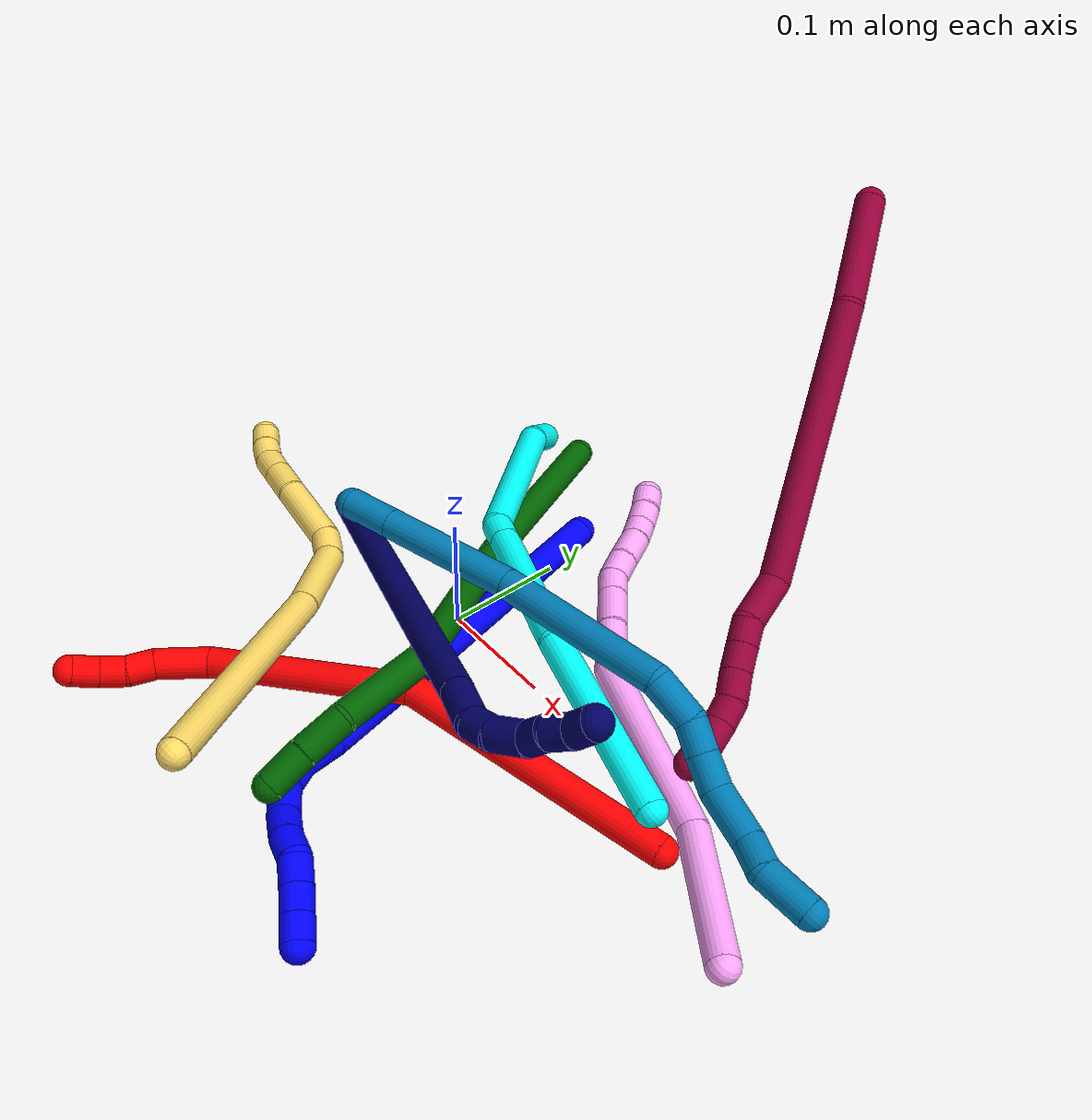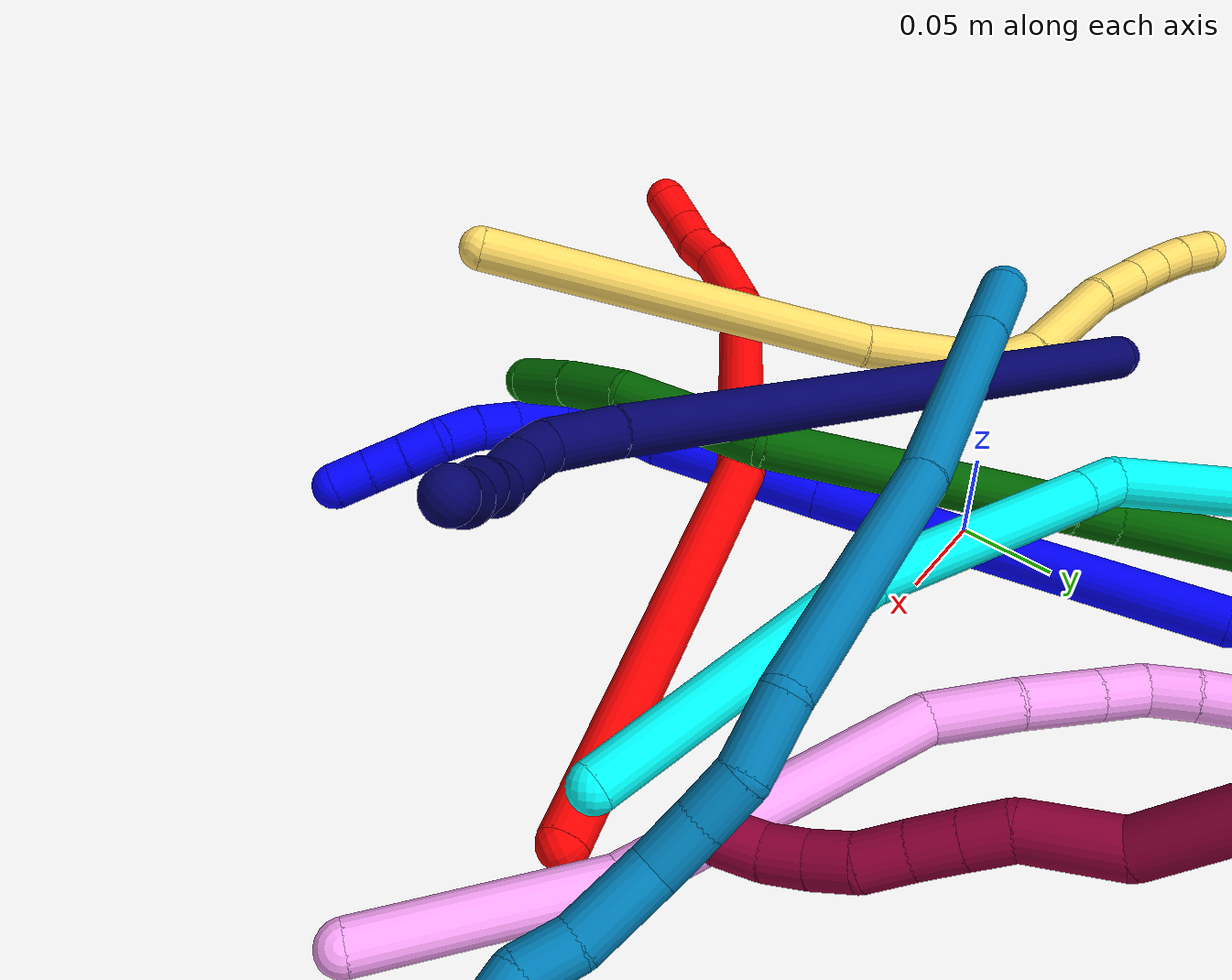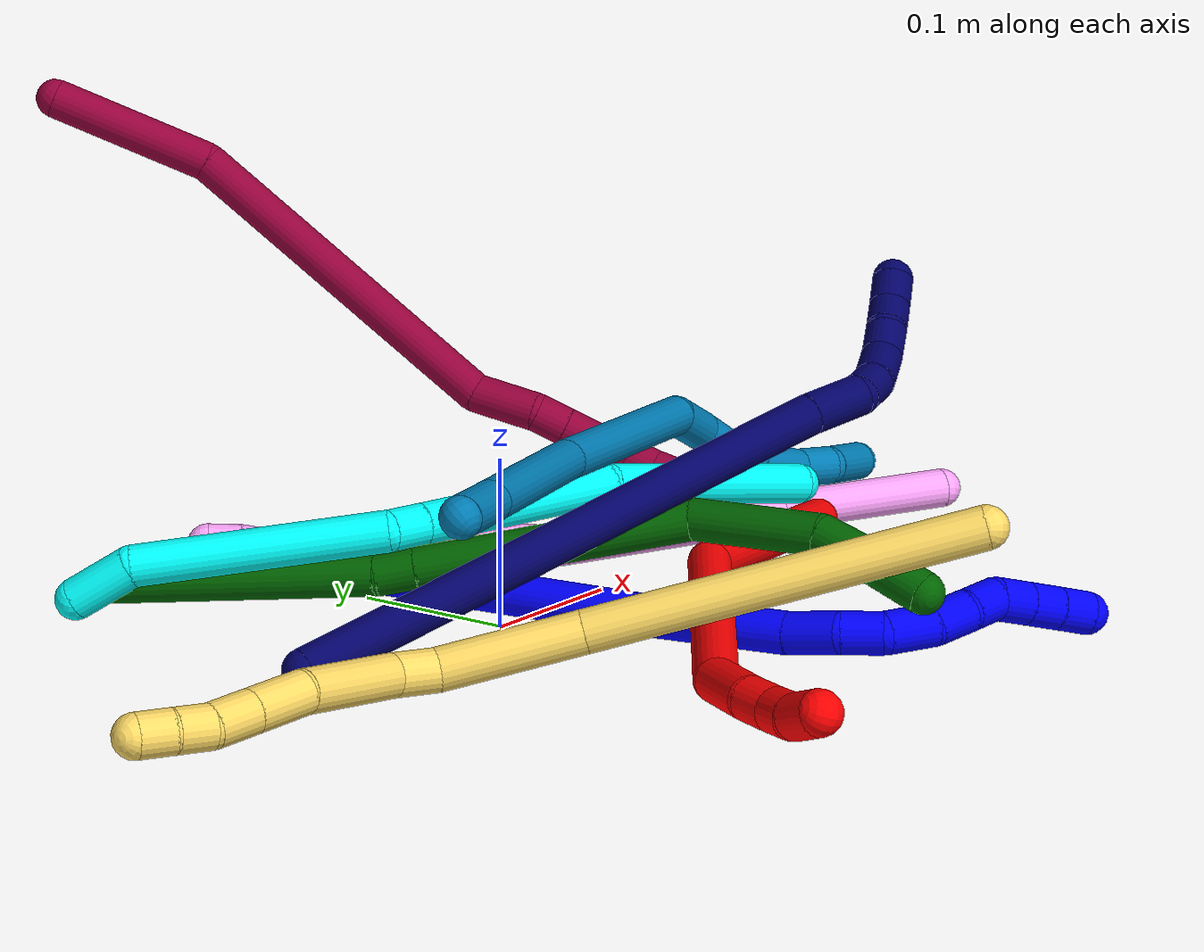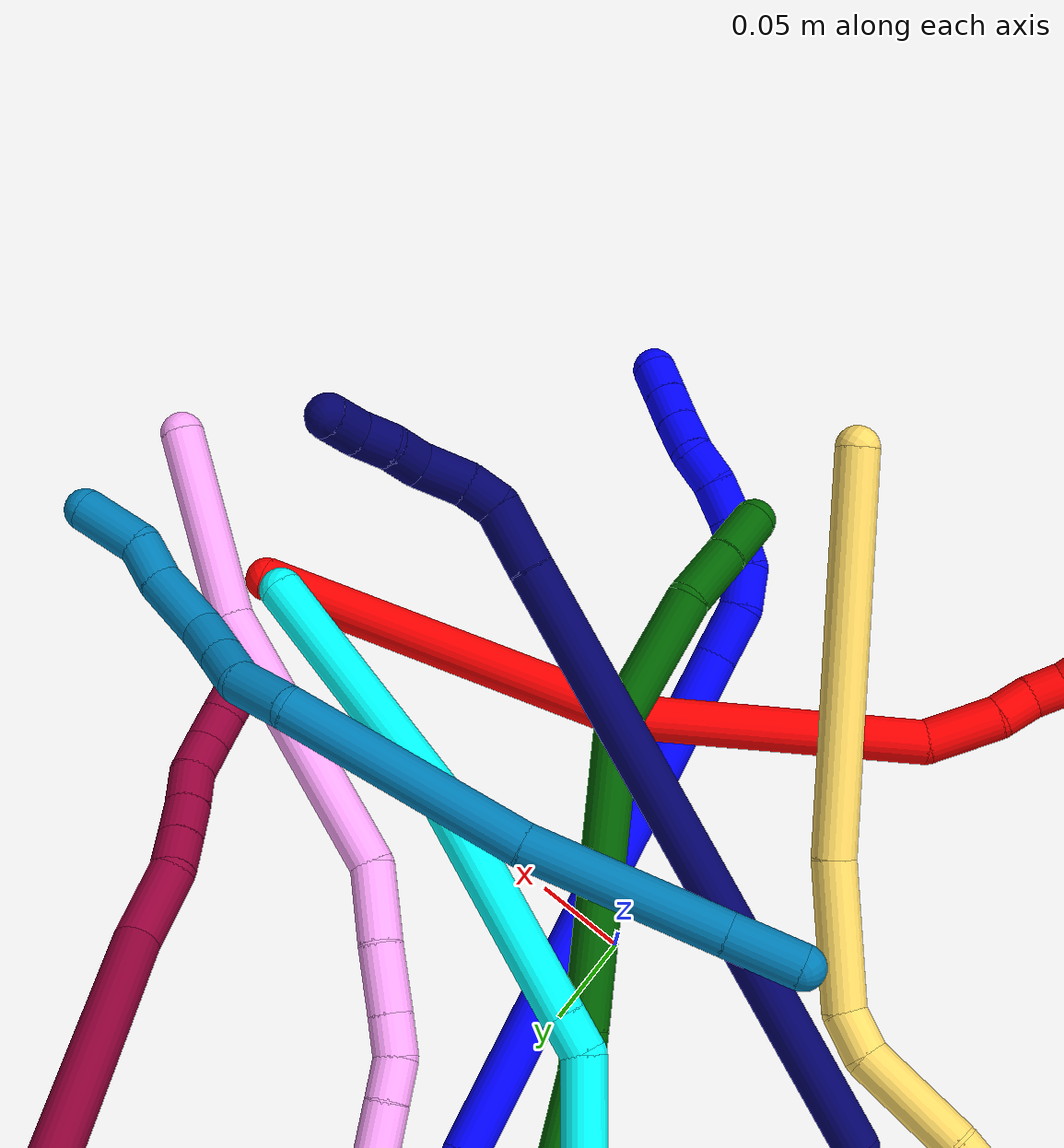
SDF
<sdf version="1.7">
 <world name="default">
  <plugin name="TubeGeneratorPlugin" filename="libtube_generator_plugin.so"/>
  <model name="photoneo_s_sensor">
   <static>1</static>
   <pose>0 0 2 1.57079 1.57079 3.14159</pose>
   <link name="link">
    <inertial><mass>0.1</mass></inertial>
    <sensor name="sensor" type="depth">
     <update_rate>30</update_rate>
     <camera>
      <horizontal_fov>1.22</horizontal_fov>
      <image><width>1920</width><height>1200</height><format>B8G8R8</format></image>
      <clip><near>0.1</near><far>4</far></clip>
      <depth_camera><output>points</output></depth_camera>
     </camera>
     <plugin name="camera_plugin" filename="libgazebo_ros_depth_camera.so">
      <baseline>0.2</baseline>
      <alwaysOn>1</alwaysOn>
      <updateRate>0.0</updateRate>
      <cameraName>camera_ir</cameraName>
      <imageTopicName>/camera/color/image_raw</imageTopicName>
      <cameraInfoTopicName>/camera/color/camera_info</cameraInfoTopicName>
      <depthImageTopicName>/camera/depth/image_raw</depthImageTopicName>
      <depthImageCameraInfoTopicName>/camera/depth/camera_info</depthImageCameraInfoTopicName>
      <pointCloudTopicName>/camera/depth/points</pointCloudTopicName>
      <frameName>fr_optical</frameName>
      <pointCloudCutoff>0.1</pointCloudCutoff>
      <pointCloudCutoffMax>2.0</pointCloudCutoffMax>
      <distortionK1>0</distortionK1>
      <distortionK2>0</distortionK2>
      <distortionK3>0</distortionK3>
      <distortionT1>0</distortionT1>
      <distortionT2>0</distortionT2>
      <CxPrime>0</CxPrime>
      <Cx>0</Cx>
      <Cy>0</Cy>
      <focalLength>0</focalLength>
      <hackBaseline>0</hackBaseline>
     </plugin>
    </sensor>
   </link>
  </model>
  <gravity>0 0 -9.8</gravity>
  <magnetic_field>6e-06 2.3e-05 -4.2e-05</magnetic_field>
  <atmosphere type="adiabatic"/>
  <physics name="default_physics" default="0" type="ode">
   <max_step_size>0.003</max_step_size>
   <real_time_factor>1</real_time_factor>
   <real_time_update_rate>1000</real_time_update_rate>
   <max_contacts>10000</max_contacts>
   <ode>
    <solver>
     <type>quick</type>
     <iters>100</iters>
     <sor>1.3</sor>
     <use_dynamic_moi_rescaling>0</use_dynamic_moi_rescaling>
    </solver>
    <constraints>
     <contact_max_correcting_vel>0</contact_max_correcting_vel>
     <contact_surface_layer>0.001</contact_surface_layer>
     <cfm>0</cfm>
     <erp>0.2</erp>
    </constraints>
   </ode>
  </physics>
  <scene><ambient>0.4 0.4 0.4 1</ambient><background>0.7 0.7 0.7 1</background><shadows>0</shadows></scene>
  <audio><device>default</device></audio>
  <spherical_coordinates>
   <surface_model>EARTH_WGS84</surface_model>
   <latitude_deg>0</latitude_deg>
   <longitude_deg>0</longitude_deg>
   <elevation>0</elevation>
   <heading_deg>0</heading_deg>
  </spherical_coordinates>
  <model name="bin">
   <static>1</static>
   <link name="bottom">
    <collision name="collision-bottom">
     <pose>0 0 -0.01 0 -0 0</pose>
     <geometry><box><size>0.8 0.6 0.02</size></box></geometry>
     <surface>
      <friction><ode><mu>100</mu><mu2>100</mu2></ode></friction>
      <contact><collide_bitmask>65535</collide_bitmask></contact>
     </surface>
    </collision>
   </link>
   <link name="west_wall">
    <collision name="collision-west_wall">
     <pose>-0.41 0 0.1 0 -0 0</pose>
     <geometry><box><size>0.02 0.6 0.2</size></box></geometry>
     <surface>
      <friction><ode><mu>100</mu><mu2>100</mu2></ode></friction>
      <contact><collide_bitmask>65535</collide_bitmask></contact>
     </surface>
    </collision>
   </link>
   <link name="east_wall">
    <collision name="collision-east_wall">
     <pose>0.41 0 0.1 0 -0 0</pose>
     <geometry><box><size>0.02 0.6 0.2</size></box></geometry>
     <surface>
      <friction><ode><mu>100</mu><mu2>100</mu2></ode></friction>
      <contact><collide_bitmask>65535</collide_bitmask></contact>
     </surface>
    </collision>
   </link>
   <link name="south_wall">
    <collision name="collision-south_wall">
     <pose>0 -0.31 0.1 0 -0 0</pose>
     <geometry><box><size>0.8 0.02 0.2</size></box></geometry>
     <surface>
      <friction><ode><mu>100</mu><mu2>100</mu2></ode></friction>
      <contact><collide_bitmask>65535</collide_bitmask></contact>
     </surface>
    </collision>
   </link>
   <link name="north_wall">
    <collision name="collision-north_wall">
     <pose>0 0.31 0.1 0 -0 0</pose>
     <geometry><box><size>0.8 0.02 0.2</size></box></geometry>
     <surface>
      <friction><ode><mu>100</mu><mu2>100</mu2></ode></friction>
      <contact><collide_bitmask>65535</collide_bitmask></contact>
     </surface>
    </collision>
   </link>
  </model>
  <model name="1">
   <static>0</static>
   <link name="1">
    <collision name="collision-cylinder-e_1_1_4">
     <pose>0.025267 -0.062573 0.082426 0.649323 0.239471 0.080942</pose>
     <geometry><cylinder><radius>0.0125</radius><length>0.213053</length></cylinder></geometry>
     <surface>
      <friction><ode><mu>1.16</mu><mu2>1.16</mu2><slip1>0</slip1><slip2>0</slip2></ode></friction>
      <contact><ode><kp>1e+06</kp><kd>1</kd><max_vel>0</max_vel><min_depth>0.001</min_depth></ode></contact>
     </surface>
    </collision>
    <visual name="visual-cylinder-e_1_1_4">
     <pose>0.025267 -0.062573 0.082426 0.649323 0.239471 0.080942</pose>
     <geometry><cylinder><radius>0.0125</radius><length>0.213053</length></cylinder></geometry>
     <material><ambient>0 0 1 1</ambient></material>
    </visual>
    <collision name="collision-cylinder-e_2_4_5">
     <pose>0.062817 -0.152075 0.201408 0.634923 0.264211 0.087266</pose>
     <geometry><cylinder><radius>0.0125</radius><length>0.09407</length></cylinder></geometry>
     <surface>
      <friction><ode><mu>1.16</mu><mu2>1.16</mu2><slip1>0</slip1><slip2>0</slip2></ode></friction>
      <contact><ode><kp>1e+06</kp><kd>1</kd><max_vel>0</max_vel><min_depth>0.001</min_depth></ode></contact>
     </surface>
    </collision>
    <visual name="visual-cylinder-e_2_4_5">
     <pose>0.062817 -0.152075 0.201408 0.634923 0.264211 0.087266</pose>
     <geometry><cylinder><radius>0.0125</radius><length>0.09407</length></cylinder></geometry>
     <material><ambient>0 0 1 1</ambient></material>
    </visual>
    <collision name="collision-cylinder-e_3_5_6">
     <pose>0.080739 -0.186548 0.25058 0.538844 0.366276 0.102199</pose>
     <geometry><cylinder><radius>0.0125</radius><length>0.031491</length></cylinder></geometry>
     <surface>
      <friction><ode><mu>1.16</mu><mu2>1.16</mu2><slip1>0</slip1><slip2>0</slip2></ode></friction>
      <contact><ode><kp>1e+06</kp><kd>1</kd><max_vel>0</max_vel><min_depth>0.001</min_depth></ode></contact>
     </surface>
    </collision>
    <visual name="visual-cylinder-e_3_5_6">
     <pose>0.080739 -0.186548 0.25058 0.538844 0.366276 0.102199</pose>
     <geometry><cylinder><radius>0.0125</radius><length>0.031491</length></cylinder></geometry>
     <material><ambient>0 0 1 1</ambient></material>
    </visual>
    <collision name="collision-cylinder-e_4_6_7">
     <pose>0.091578 -0.202815 0.270044 0.905369 0.438454 0.215892</pose>
     <geometry><cylinder><radius>0.0125</radius><length>0.024494</length></cylinder></geometry>
     <surface>
      <friction><ode><mu>1.16</mu><mu2>1.16</mu2><slip1>0</slip1><slip2>0</slip2></ode></friction>
      <contact><ode><kp>1e+06</kp><kd>1</kd><max_vel>0</max_vel><min_depth>0.001</min_depth></ode></contact>
     </surface>
    </collision>
    <visual name="visual-cylinder-e_4_6_7">
     <pose>0.091578 -0.202815 0.270044 0.905369 0.438454 0.215892</pose>
     <geometry><cylinder><radius>0.0125</radius><length>0.024494</length></cylinder></geometry>
     <material><ambient>0 0 1 1</ambient></material>
    </visual>
    <collision name="collision-cylinder-e_5_7_8">
     <pose>0.105685 -0.223446 0.278947 1.39973 0.635173 0.540071</pose>
     <geometry><cylinder><radius>0.0125</radius><length>0.030027</length></cylinder></geometry>
     <surface>
      <friction><ode><mu>1.16</mu><mu2>1.16</mu2><slip1>0</slip1><slip2>0</slip2></ode></friction>
      <contact><ode><kp>1e+06</kp><kd>1</kd><max_vel>0</max_vel><min_depth>0.001</min_depth></ode></contact>
     </surface>
    </collision>
    <visual name="visual-cylinder-e_5_7_8">
     <pose>0.105685 -0.223446 0.278947 1.39973 0.635173 0.540071</pose>
     <geometry><cylinder><radius>0.0125</radius><length>0.030027</length></cylinder></geometry>
     <material><ambient>0 0 1 1</ambient></material>
    </visual>
    <collision name="collision-cylinder-e_6_8_9">
     <pose>0.123259 -0.243387 0.281354 1.52739 0.822908 0.791547</pose>
     <geometry><cylinder><radius>0.0125</radius><length>0.023643</length></cylinder></geometry>
     <surface>
      <friction><ode><mu>1.16</mu><mu2>1.16</mu2><slip1>0</slip1><slip2>0</slip2></ode></friction>
      <contact><ode><kp>1e+06</kp><kd>1</kd><max_vel>0</max_vel><min_depth>0.001</min_depth></ode></contact>
     </surface>
    </collision>
    <visual name="visual-cylinder-e_6_8_9">
     <pose>0.123259 -0.243387 0.281354 1.52739 0.822908 0.791547</pose>
     <geometry><cylinder><radius>0.0125</radius><length>0.023643</length></cylinder></geometry>
     <material><ambient>0 0 1 1</ambient></material>
    </visual>
    <collision name="collision-cylinder-e_7_9_10">
     <pose>0.139278 -0.259156 0.279861 1.80443 0.746237 0.920153</pose>
     <geometry><cylinder><radius>0.0125</radius><length>0.021661</length></cylinder></geometry>
     <surface>
      <friction><ode><mu>1.16</mu><mu2>1.16</mu2><slip1>0</slip1><slip2>0</slip2></ode></friction>
      <contact><ode><kp>1e+06</kp><kd>1</kd><max_vel>0</max_vel><min_depth>0.001</min_depth></ode></contact>
     </surface>
    </collision>
    <visual name="visual-cylinder-e_7_9_10">
     <pose>0.139278 -0.259156 0.279861 1.80443 0.746237 0.920153</pose>
     <geometry><cylinder><radius>0.0125</radius><length>0.021661</length></cylinder></geometry>
     <material><ambient>0 0 1 1</ambient></material>
    </visual>
    <collision name="collision-cylinder-e_8_10_11">
     <pose>0.150179 -0.276843 0.278378 1.53484 0.342308 0.330438</pose>
     <geometry><cylinder><radius>0.0125</radius><length>0.02114</length></cylinder></geometry>
     <surface>
      <friction><ode><mu>1.16</mu><mu2>1.16</mu2><slip1>0</slip1><slip2>0</slip2></ode></friction>
      <contact><ode><kp>1e+06</kp><kd>1</kd><max_vel>0</max_vel><min_depth>0.001</min_depth></ode></contact>
     </surface>
    </collision>
    <visual name="visual-cylinder-e_8_10_11">
     <pose>0.150179 -0.276843 0.278378 1.53484 0.342308 0.330438</pose>
     <geometry><cylinder><radius>0.0125</radius><length>0.02114</length></cylinder></geometry>
     <material><ambient>0 0 1 1</ambient></material>
    </visual>
    <collision name="collision-cylinder-e_9_11_12">
     <pose>0.157078 -0.296242 0.279497 1.49049 0.339811 0.314008</pose>
     <geometry><cylinder><radius>0.0125</radius><length>0.020108</length></cylinder></geometry>
     <surface>
      <friction><ode><mu>1.16</mu><mu2>1.16</mu2><slip1>0</slip1><slip2>0</slip2></ode></friction>
      <contact><ode><kp>1e+06</kp><kd>1</kd><max_vel>0</max_vel><min_depth>0.001</min_depth></ode></contact>
     </surface>
    </collision>
    <visual name="visual-cylinder-e_9_11_12">
     <pose>0.157078 -0.296242 0.279497 1.49049 0.339811 0.314008</pose>
     <geometry><cylinder><radius>0.0125</radius><length>0.020108</length></cylinder></geometry>
     <material><ambient>0 0 1 1</ambient></material>
    </visual>
    <collision name="collision-cylinder-e_10_12_2">
     <pose>0.163759 -0.315259 0.280963 1.49716 0.334002 0.310665</pose>
     <geometry><cylinder><radius>0.0125</radius><length>0.020312</length></cylinder></geometry>
     <surface>
      <friction><ode><mu>1.16</mu><mu2>1.16</mu2><slip1>0</slip1><slip2>0</slip2></ode></friction>
      <contact><ode><kp>1e+06</kp><kd>1</kd><max_vel>0</max_vel><min_depth>0.001</min_depth></ode></contact>
     </surface>
    </collision>
    <visual name="visual-cylinder-e_10_12_2">
     <pose>0.163759 -0.315259 0.280963 1.49716 0.334002 0.310665</pose>
     <geometry><cylinder><radius>0.0125</radius><length>0.020312</length></cylinder></geometry>
     <material><ambient>0 0 1 1</ambient></material>
    </visual>
    <collision name="collision-sphere-2">
     <pose>0.167088 -0.324828 0.281669 0 -0 0</pose>
     <geometry><sphere><radius>0.0125</radius></sphere></geometry>
     <surface>
      <friction><ode><mu>1.16</mu><mu2>1.16</mu2><slip1>0</slip1><slip2>0</slip2></ode></friction>
      <contact><ode><kp>1e+06</kp><kd>1</kd><max_vel>0</max_vel><min_depth>0.001</min_depth></ode></contact>
     </surface>
    </collision>
    <visual name="visual-sphere-2">
     <pose>0.167088 -0.324828 0.281669 0 -0 0</pose>
     <geometry><sphere><radius>0.0125</radius></sphere></geometry>
     <material><ambient>0 0 1 1</ambient></material>
    </visual>
    <collision name="collision-sphere-12">
     <pose>0.160429 -0.30569 0.280257 0 -0 0</pose>
     <geometry><sphere><radius>0.0125</radius></sphere></geometry>
     <surface>
      <friction><ode><mu>1.16</mu><mu2>1.16</mu2><slip1>0</slip1><slip2>0</slip2></ode></friction>
      <contact><ode><kp>1e+06</kp><kd>1</kd><max_vel>0</max_vel><min_depth>0.001</min_depth></ode></contact>
     </surface>
    </collision>
    <visual name="visual-sphere-12">
     <pose>0.160429 -0.30569 0.280257 0 -0 0</pose>
     <geometry><sphere><radius>0.0125</radius></sphere></geometry>
     <material><ambient>0 0 1 1</ambient></material>
    </visual>
    <collision name="collision-sphere-11">
     <pose>0.153727 -0.286793 0.278736 0 -0 0</pose>
     <geometry><sphere><radius>0.0125</radius></sphere></geometry>
     <surface>
      <friction><ode><mu>1.16</mu><mu2>1.16</mu2><slip1>0</slip1><slip2>0</slip2></ode></friction>
      <contact><ode><kp>1e+06</kp><kd>1</kd><max_vel>0</max_vel><min_depth>0.001</min_depth></ode></contact>
     </surface>
    </collision>
    <visual name="visual-sphere-11">
     <pose>0.153727 -0.286793 0.278736 0 -0 0</pose>
     <geometry><sphere><radius>0.0125</radius></sphere></geometry>
     <material><ambient>0 0 1 1</ambient></material>
    </visual>
    <collision name="collision-sphere-10">
     <pose>0.146631 -0.266892 0.27802 0 -0 0</pose>
     <geometry><sphere><radius>0.0125</radius></sphere></geometry>
     <surface>
      <friction><ode><mu>1.16</mu><mu2>1.16</mu2><slip1>0</slip1><slip2>0</slip2></ode></friction>
      <contact><ode><kp>1e+06</kp><kd>1</kd><max_vel>0</max_vel><min_depth>0.001</min_depth></ode></contact>
     </surface>
    </collision>
    <visual name="visual-sphere-10">
     <pose>0.146631 -0.266892 0.27802 0 -0 0</pose>
     <geometry><sphere><radius>0.0125</radius></sphere></geometry>
     <material><ambient>0 0 1 1</ambient></material>
    </visual>
    <collision name="collision-sphere-9">
     <pose>0.131926 -0.251419 0.281702 0 -0 0</pose>
     <geometry><sphere><radius>0.0125</radius></sphere></geometry>
     <surface>
      <friction><ode><mu>1.16</mu><mu2>1.16</mu2><slip1>0</slip1><slip2>0</slip2></ode></friction>
      <contact><ode><kp>1e+06</kp><kd>1</kd><max_vel>0</max_vel><min_depth>0.001</min_depth></ode></contact>
     </surface>
    </collision>
    <visual name="visual-sphere-9">
     <pose>0.131926 -0.251419 0.281702 0 -0 0</pose>
     <geometry><sphere><radius>0.0125</radius></sphere></geometry>
     <material><ambient>0 0 1 1</ambient></material>
    </visual>
    <collision name="collision-sphere-4">
     <pose>0.050534 -0.125146 0.164853 0 -0 0</pose>
     <geometry><sphere><radius>0.0125</radius></sphere></geometry>
     <surface>
      <friction><ode><mu>1.16</mu><mu2>1.16</mu2><slip1>0</slip1><slip2>0</slip2></ode></friction>
      <contact><ode><kp>1e+06</kp><kd>1</kd><max_vel>0</max_vel><min_depth>0.001</min_depth></ode></contact>
     </surface>
    </collision>
    <visual name="visual-sphere-4">
     <pose>0.050534 -0.125146 0.164853 0 -0 0</pose>
     <geometry><sphere><radius>0.0125</radius></sphere></geometry>
     <material><ambient>0 0 1 1</ambient></material>
    </visual>
    <collision name="collision-sphere-1">
     <geometry><sphere><radius>0.0125</radius></sphere></geometry>
     <surface>
      <friction><ode><mu>1.16</mu><mu2>1.16</mu2><slip1>0</slip1><slip2>0</slip2></ode></friction>
      <contact><ode><kp>1e+06</kp><kd>1</kd><max_vel>0</max_vel><min_depth>0.001</min_depth></ode></contact>
     </surface>
    </collision>
    <visual name="visual-sphere-1">
     <geometry><sphere><radius>0.0125</radius></sphere></geometry>
     <material><ambient>0 0 1 1</ambient></material>
    </visual>
    <collision name="collision-sphere-8">
     <pose>0.114592 -0.235355 0.281005 0 -0 0</pose>
     <geometry><sphere><radius>0.0125</radius></sphere></geometry>
     <surface>
      <friction><ode><mu>1.16</mu><mu2>1.16</mu2><slip1>0</slip1><slip2>0</slip2></ode></friction>
      <contact><ode><kp>1e+06</kp><kd>1</kd><max_vel>0</max_vel><min_depth>0.001</min_depth></ode></contact>
     </surface>
    </collision>
    <visual name="visual-sphere-8">
     <pose>0.114592 -0.235355 0.281005 0 -0 0</pose>
     <geometry><sphere><radius>0.0125</radius></sphere></geometry>
     <material><ambient>0 0 1 1</ambient></material>
    </visual>
    <collision name="collision-sphere-5">
     <pose>0.0751 -0.179004 0.237962 0 -0 0</pose>
     <geometry><sphere><radius>0.0125</radius></sphere></geometry>
     <surface>
      <friction><ode><mu>1.16</mu><mu2>1.16</mu2><slip1>0</slip1><slip2>0</slip2></ode></friction>
      <contact><ode><kp>1e+06</kp><kd>1</kd><max_vel>0</max_vel><min_depth>0.001</min_depth></ode></contact>
     </surface>
    </collision>
    <visual name="visual-sphere-5">
     <pose>0.0751 -0.179004 0.237962 0 -0 0</pose>
     <geometry><sphere><radius>0.0125</radius></sphere></geometry>
     <material><ambient>0 0 1 1</ambient></material>
    </visual>
    <collision name="collision-sphere-6">
     <pose>0.086378 -0.194092 0.263198 0 -0 0</pose>
     <geometry><sphere><radius>0.0125</radius></sphere></geometry>
     <surface>
      <friction><ode><mu>1.16</mu><mu2>1.16</mu2><slip1>0</slip1><slip2>0</slip2></ode></friction>
      <contact><ode><kp>1e+06</kp><kd>1</kd><max_vel>0</max_vel><min_depth>0.001</min_depth></ode></contact>
     </surface>
    </collision>
    <visual name="visual-sphere-6">
     <pose>0.086378 -0.194092 0.263198 0 -0 0</pose>
     <geometry><sphere><radius>0.0125</radius></sphere></geometry>
     <material><ambient>0 0 1 1</ambient></material>
    </visual>
    <collision name="collision-sphere-7">
     <pose>0.096777 -0.211537 0.27689 0 -0 0</pose>
     <geometry><sphere><radius>0.0125</radius></sphere></geometry>
     <surface>
      <friction><ode><mu>1.16</mu><mu2>1.16</mu2><slip1>0</slip1><slip2>0</slip2></ode></friction>
      <contact><ode><kp>1e+06</kp><kd>1</kd><max_vel>0</max_vel><min_depth>0.001</min_depth></ode></contact>
     </surface>
    </collision>
    <visual name="visual-sphere-7">
     <pose>0.096777 -0.211537 0.27689 0 -0 0</pose>
     <geometry><sphere><radius>0.0125</radius></sphere></geometry>
     <material><ambient>0 0 1 1</ambient></material>
    </visual>
    <inertial>
     <pose>0.069685 -0.14954 0.178631 0 -0 0</pose>
     <mass>0.5</mass>
     <inertia>
      <ixx>0.000961</ixx>
      <ixy>0</ixy>
      <ixz>0</ixz>
      <iyy>0.000775</iyy>
      <iyz>0</iyz>
      <izz>0.000334</izz>
     </inertia>
    </inertial>
   </link>
   <pose>-0.006734 0.139304 0.017554 1.33873 -0.96665 -0.274002</pose>
  </model>
  <model name="2">
   <static>0</static>
   <link name="2">
    <collision name="collision-cylinder-e_1_1_4">
     <pose>-0.080257 -0.01519 -0.075407 2.94281 -0.806613 -2.68243</pose>
     <geometry><cylinder><radius>0.0125</radius><length>0.222335</length></cylinder></geometry>
     <surface>
      <friction><ode><mu>1.16</mu><mu2>1.16</mu2><slip1>0</slip1><slip2>0</slip2></ode></friction>
      <contact><ode><kp>1e+06</kp><kd>1</kd><max_vel>0</max_vel><min_depth>0.001</min_depth></ode></contact>
     </surface>
    </collision>
    <visual name="visual-cylinder-e_1_1_4">
     <pose>-0.080257 -0.01519 -0.075407 2.94281 -0.806613 -2.68243</pose>
     <geometry><cylinder><radius>0.0125</radius><length>0.222335</length></cylinder></geometry>
     <material><ambient>1 0 0 1</ambient></material>
    </visual>
    <collision name="collision-cylinder-e_2_4_5">
     <pose>-0.236377 -0.054189 -0.179216 2.44396 -1.11637 -2.08678</pose>
     <geometry><cylinder><radius>0.0125</radius><length>0.168863</length></cylinder></geometry>
     <surface>
      <friction><ode><mu>1.16</mu><mu2>1.16</mu2><slip1>0</slip1><slip2>0</slip2></ode></friction>
      <contact><ode><kp>1e+06</kp><kd>1</kd><max_vel>0</max_vel><min_depth>0.001</min_depth></ode></contact>
     </surface>
    </collision>
    <visual name="visual-cylinder-e_2_4_5">
     <pose>-0.236377 -0.054189 -0.179216 2.44396 -1.11637 -2.08678</pose>
     <geometry><cylinder><radius>0.0125</radius><length>0.168863</length></cylinder></geometry>
     <material><ambient>1 0 0 1</ambient></material>
    </visual>
    <collision name="collision-cylinder-e_3_5_6">
     <pose>-0.333715 -0.078279 -0.208408 2.79856 -1.53176 -2.78518</pose>
     <geometry><cylinder><radius>0.0125</radius><length>0.042984</length></cylinder></geometry>
     <surface>
      <friction><ode><mu>1.16</mu><mu2>1.16</mu2><slip1>0</slip1><slip2>0</slip2></ode></friction>
      <contact><ode><kp>1e+06</kp><kd>1</kd><max_vel>0</max_vel><min_depth>0.001</min_depth></ode></contact>
     </surface>
    </collision>
    <visual name="visual-cylinder-e_3_5_6">
     <pose>-0.333715 -0.078279 -0.208408 2.79856 -1.53176 -2.78518</pose>
     <geometry><cylinder><radius>0.0125</radius><length>0.042984</length></cylinder></geometry>
     <material><ambient>1 0 0 1</ambient></material>
    </visual>
    <collision name="collision-cylinder-e_4_6_7">
     <pose>-0.365902 -0.07873 -0.206915 0.074072 -1.36021 -0.059922</pose>
     <geometry><cylinder><radius>0.0125</radius><length>0.021906</length></cylinder></geometry>
     <surface>
      <friction><ode><mu>1.16</mu><mu2>1.16</mu2><slip1>0</slip1><slip2>0</slip2></ode></friction>
      <contact><ode><kp>1e+06</kp><kd>1</kd><max_vel>0</max_vel><min_depth>0.001</min_depth></ode></contact>
     </surface>
    </collision>
    <visual name="visual-cylinder-e_4_6_7">
     <pose>-0.365902 -0.07873 -0.206915 0.074072 -1.36021 -0.059922</pose>
     <geometry><cylinder><radius>0.0125</radius><length>0.021906</length></cylinder></geometry>
     <material><ambient>1 0 0 1</ambient></material>
    </visual>
    <collision name="collision-cylinder-e_5_7_8">
     <pose>-0.387208 -0.078386 -0.204801 -1.89024 -1.51981 1.84145</pose>
     <geometry><cylinder><radius>0.0125</radius><length>0.021217</length></cylinder></geometry>
     <surface>
      <friction><ode><mu>1.16</mu><mu2>1.16</mu2><slip1>0</slip1><slip2>0</slip2></ode></friction>
      <contact><ode><kp>1e+06</kp><kd>1</kd><max_vel>0</max_vel><min_depth>0.001</min_depth></ode></contact>
     </surface>
    </collision>
    <visual name="visual-cylinder-e_5_7_8">
     <pose>-0.387208 -0.078386 -0.204801 -1.89024 -1.51981 1.84145</pose>
     <geometry><cylinder><radius>0.0125</radius><length>0.021217</length></cylinder></geometry>
     <material><ambient>1 0 0 1</ambient></material>
    </visual>
    <collision name="collision-cylinder-e_6_8_2">
     <pose>-0.408484 -0.074096 -0.204326 -1.40178 -1.22635 1.07163</pose>
     <geometry><cylinder><radius>0.0125</radius><length>0.022695</length></cylinder></geometry>
     <surface>
      <friction><ode><mu>1.16</mu><mu2>1.16</mu2><slip1>0</slip1><slip2>0</slip2></ode></friction>
      <contact><ode><kp>1e+06</kp><kd>1</kd><max_vel>0</max_vel><min_depth>0.001</min_depth></ode></contact>
     </surface>
    </collision>
    <visual name="visual-cylinder-e_6_8_2">
     <pose>-0.408484 -0.074096 -0.204326 -1.40178 -1.22635 1.07163</pose>
     <geometry><cylinder><radius>0.0125</radius><length>0.022695</length></cylinder></geometry>
     <material><ambient>1 0 0 1</ambient></material>
    </visual>
    <collision name="collision-sphere-2">
     <pose>-0.419165 -0.070319 -0.203682 0 -0 0</pose>
     <geometry><sphere><radius>0.0125</radius></sphere></geometry>
     <surface>
      <friction><ode><mu>1.16</mu><mu2>1.16</mu2><slip1>0</slip1><slip2>0</slip2></ode></friction>
      <contact><ode><kp>1e+06</kp><kd>1</kd><max_vel>0</max_vel><min_depth>0.001</min_depth></ode></contact>
     </surface>
    </collision>
    <visual name="visual-sphere-2">
     <pose>-0.419165 -0.070319 -0.203682 0 -0 0</pose>
     <geometry><sphere><radius>0.0125</radius></sphere></geometry>
     <material><ambient>1 0 0 1</ambient></material>
    </visual>
    <collision name="collision-sphere-4">
     <pose>-0.160514 -0.030381 -0.150815 0 -0 0</pose>
     <geometry><sphere><radius>0.0125</radius></sphere></geometry>
     <surface>
      <friction><ode><mu>1.16</mu><mu2>1.16</mu2><slip1>0</slip1><slip2>0</slip2></ode></friction>
      <contact><ode><kp>1e+06</kp><kd>1</kd><max_vel>0</max_vel><min_depth>0.001</min_depth></ode></contact>
     </surface>
    </collision>
    <visual name="visual-sphere-4">
     <pose>-0.160514 -0.030381 -0.150815 0 -0 0</pose>
     <geometry><sphere><radius>0.0125</radius></sphere></geometry>
     <material><ambient>1 0 0 1</ambient></material>
    </visual>
    <collision name="collision-sphere-1">
     <geometry><sphere><radius>0.0125</radius></sphere></geometry>
     <surface>
      <friction><ode><mu>1.16</mu><mu2>1.16</mu2><slip1>0</slip1><slip2>0</slip2></ode></friction>
      <contact><ode><kp>1e+06</kp><kd>1</kd><max_vel>0</max_vel><min_depth>0.001</min_depth></ode></contact>
     </surface>
    </collision>
    <visual name="visual-sphere-1">
     <geometry><sphere><radius>0.0125</radius></sphere></geometry>
     <material><ambient>1 0 0 1</ambient></material>
    </visual>
    <collision name="collision-sphere-8">
     <pose>-0.397803 -0.077873 -0.204971 0 -0 0</pose>
     <geometry><sphere><radius>0.0125</radius></sphere></geometry>
     <surface>
      <friction><ode><mu>1.16</mu><mu2>1.16</mu2><slip1>0</slip1><slip2>0</slip2></ode></friction>
      <contact><ode><kp>1e+06</kp><kd>1</kd><max_vel>0</max_vel><min_depth>0.001</min_depth></ode></contact>
     </surface>
    </collision>
    <visual name="visual-sphere-8">
     <pose>-0.397803 -0.077873 -0.204971 0 -0 0</pose>
     <geometry><sphere><radius>0.0125</radius></sphere></geometry>
     <material><ambient>1 0 0 1</ambient></material>
    </visual>
    <collision name="collision-sphere-5">
     <pose>-0.31224 -0.077997 -0.207618 0 -0 0</pose>
     <geometry><sphere><radius>0.0125</radius></sphere></geometry>
     <surface>
      <friction><ode><mu>1.16</mu><mu2>1.16</mu2><slip1>0</slip1><slip2>0</slip2></ode></friction>
      <contact><ode><kp>1e+06</kp><kd>1</kd><max_vel>0</max_vel><min_depth>0.001</min_depth></ode></contact>
     </surface>
    </collision>
    <visual name="visual-sphere-5">
     <pose>-0.31224 -0.077997 -0.207618 0 -0 0</pose>
     <geometry><sphere><radius>0.0125</radius></sphere></geometry>
     <material><ambient>1 0 0 1</ambient></material>
    </visual>
    <collision name="collision-sphere-6">
     <pose>-0.355191 -0.078561 -0.209198 0 -0 0</pose>
     <geometry><sphere><radius>0.0125</radius></sphere></geometry>
     <surface>
      <friction><ode><mu>1.16</mu><mu2>1.16</mu2><slip1>0</slip1><slip2>0</slip2></ode></friction>
      <contact><ode><kp>1e+06</kp><kd>1</kd><max_vel>0</max_vel><min_depth>0.001</min_depth></ode></contact>
     </surface>
    </collision>
    <visual name="visual-sphere-6">
     <pose>-0.355191 -0.078561 -0.209198 0 -0 0</pose>
     <geometry><sphere><radius>0.0125</radius></sphere></geometry>
     <material><ambient>1 0 0 1</ambient></material>
    </visual>
    <collision name="collision-sphere-7">
     <pose>-0.376613 -0.0789 -0.204631 0 -0 0</pose>
     <geometry><sphere><radius>0.0125</radius></sphere></geometry>
     <surface>
      <friction><ode><mu>1.16</mu><mu2>1.16</mu2><slip1>0</slip1><slip2>0</slip2></ode></friction>
      <contact><ode><kp>1e+06</kp><kd>1</kd><max_vel>0</max_vel><min_depth>0.001</min_depth></ode></contact>
     </surface>
    </collision>
    <visual name="visual-sphere-7">
     <pose>-0.376613 -0.0789 -0.204631 0 -0 0</pose>
     <geometry><sphere><radius>0.0125</radius></sphere></geometry>
     <material><ambient>1 0 0 1</ambient></material>
    </visual>
    <inertial>
     <pose>-0.19521 -0.041924 -0.139004 0 -0 0</pose>
     <mass>0.5</mass>
     <inertia>
      <ixx>-0.001133</ixx>
      <ixy>0</ixy>
      <ixz>0</ixz>
      <iyy>0.000799</iyy>
      <iyz>0</iyz>
      <izz>0.001272</izz>
     </inertia>
    </inertial>
   </link>
   <pose>0.283619 -0.03812 0.011967 1.88528 0.058655 1.03506</pose>
  </model>
  <model name="3">
   <static>0</static>
   <link name="3">
    <collision name="collision-cylinder-e_1_1_4">
     <pose>0.001863 0.066324 -0.043086 -2.14691 0.023552 -0.043381</pose>
     <geometry><cylinder><radius>0.0125</radius><length>0.158224</length></cylinder></geometry>
     <surface>
      <friction><ode><mu>1.16</mu><mu2>1.16</mu2><slip1>0</slip1><slip2>0</slip2></ode></friction>
      <contact><ode><kp>1e+06</kp><kd>1</kd><max_vel>0</max_vel><min_depth>0.001</min_depth></ode></contact>
     </surface>
    </collision>
    <visual name="visual-cylinder-e_1_1_4">
     <pose>0.001863 0.066324 -0.043086 -2.14691 0.023552 -0.043381</pose>
     <geometry><cylinder><radius>0.0125</radius><length>0.158224</length></cylinder></geometry>
     <material><ambient>0.003922 1 0.996078 1</ambient></material>
    </visual>
    <collision name="collision-cylinder-e_2_4_5">
     <pose>0.006902 0.1938 -0.107082 -1.90027 0.049107 -0.068676</pose>
     <geometry><cylinder><radius>0.0125</radius><length>0.129414</length></cylinder></geometry>
     <surface>
      <friction><ode><mu>1.16</mu><mu2>1.16</mu2><slip1>0</slip1><slip2>0</slip2></ode></friction>
      <contact><ode><kp>1e+06</kp><kd>1</kd><max_vel>0</max_vel><min_depth>0.001</min_depth></ode></contact>
     </surface>
    </collision>
    <visual name="visual-cylinder-e_2_4_5">
     <pose>0.006902 0.1938 -0.107082 -1.90027 0.049107 -0.068676</pose>
     <geometry><cylinder><radius>0.0125</radius><length>0.129414</length></cylinder></geometry>
     <material><ambient>0.003922 1 0.996078 1</ambient></material>
    </visual>
    <collision name="collision-cylinder-e_3_5_6">
     <pose>0.010628 0.265344 -0.13155 -1.90069 0.049953 -0.069891</pose>
     <geometry><cylinder><radius>0.0125</radius><length>0.021993</length></cylinder></geometry>
     <surface>
      <friction><ode><mu>1.16</mu><mu2>1.16</mu2><slip1>0</slip1><slip2>0</slip2></ode></friction>
      <contact><ode><kp>1e+06</kp><kd>1</kd><max_vel>0</max_vel><min_depth>0.001</min_depth></ode></contact>
     </surface>
    </collision>
    <visual name="visual-cylinder-e_3_5_6">
     <pose>0.010628 0.265344 -0.13155 -1.90069 0.049953 -0.069891</pose>
     <geometry><cylinder><radius>0.0125</radius><length>0.021993</length></cylinder></geometry>
     <material><ambient>0.003922 1 0.996078 1</ambient></material>
    </visual>
    <collision name="collision-cylinder-e_4_6_7">
     <pose>-0.011058 0.347717 -0.13105 -1.51449 -0.299152 0.282988</pose>
     <geometry><cylinder><radius>0.0125</radius><length>0.150896</length></cylinder></geometry>
     <surface>
      <friction><ode><mu>1.16</mu><mu2>1.16</mu2><slip1>0</slip1><slip2>0</slip2></ode></friction>
      <contact><ode><kp>1e+06</kp><kd>1</kd><max_vel>0</max_vel><min_depth>0.001</min_depth></ode></contact>
     </surface>
    </collision>
    <visual name="visual-cylinder-e_4_6_7">
     <pose>-0.011058 0.347717 -0.13105 -1.51449 -0.299152 0.282988</pose>
     <geometry><cylinder><radius>0.0125</radius><length>0.150896</length></cylinder></geometry>
     <material><ambient>0.003922 1 0.996078 1</ambient></material>
    </visual>
    <collision name="collision-cylinder-e_5_7_2">
     <pose>-0.034954 0.437386 -0.118392 -1.11819 -0.084217 0.052713</pose>
     <geometry><cylinder><radius>0.0125</radius><length>0.039473</length></cylinder></geometry>
     <surface>
      <friction><ode><mu>1.16</mu><mu2>1.16</mu2><slip1>0</slip1><slip2>0</slip2></ode></friction>
      <contact><ode><kp>1e+06</kp><kd>1</kd><max_vel>0</max_vel><min_depth>0.001</min_depth></ode></contact>
     </surface>
    </collision>
    <visual name="visual-cylinder-e_5_7_2">
     <pose>-0.034954 0.437386 -0.118392 -1.11819 -0.084217 0.052713</pose>
     <geometry><cylinder><radius>0.0125</radius><length>0.039473</length></cylinder></geometry>
     <material><ambient>0.003922 1 0.996078 1</ambient></material>
    </visual>
    <collision name="collision-sphere-2">
     <pose>-0.036614 0.455073 -0.109792 0 -0 0</pose>
     <geometry><sphere><radius>0.0125</radius></sphere></geometry>
     <surface>
      <friction><ode><mu>1.16</mu><mu2>1.16</mu2><slip1>0</slip1><slip2>0</slip2></ode></friction>
      <contact><ode><kp>1e+06</kp><kd>1</kd><max_vel>0</max_vel><min_depth>0.001</min_depth></ode></contact>
     </surface>
    </collision>
    <visual name="visual-sphere-2">
     <pose>-0.036614 0.455073 -0.109792 0 -0 0</pose>
     <geometry><sphere><radius>0.0125</radius></sphere></geometry>
     <material><ambient>0.003922 1 0.996078 1</ambient></material>
    </visual>
    <collision name="collision-sphere-7">
     <pose>-0.033294 0.4197 -0.126993 0 -0 0</pose>
     <geometry><sphere><radius>0.0125</radius></sphere></geometry>
     <surface>
      <friction><ode><mu>1.16</mu><mu2>1.16</mu2><slip1>0</slip1><slip2>0</slip2></ode></friction>
      <contact><ode><kp>1e+06</kp><kd>1</kd><max_vel>0</max_vel><min_depth>0.001</min_depth></ode></contact>
     </surface>
    </collision>
    <visual name="visual-sphere-7">
     <pose>-0.033294 0.4197 -0.126993 0 -0 0</pose>
     <geometry><sphere><radius>0.0125</radius></sphere></geometry>
     <material><ambient>0.003922 1 0.996078 1</ambient></material>
    </visual>
    <collision name="collision-sphere-6">
     <pose>0.011177 0.275734 -0.135108 0 -0 0</pose>
     <geometry><sphere><radius>0.0125</radius></sphere></geometry>
     <surface>
      <friction><ode><mu>1.16</mu><mu2>1.16</mu2><slip1>0</slip1><slip2>0</slip2></ode></friction>
      <contact><ode><kp>1e+06</kp><kd>1</kd><max_vel>0</max_vel><min_depth>0.001</min_depth></ode></contact>
     </surface>
    </collision>
    <visual name="visual-sphere-6">
     <pose>0.011177 0.275734 -0.135108 0 -0 0</pose>
     <geometry><sphere><radius>0.0125</radius></sphere></geometry>
     <material><ambient>0.003922 1 0.996078 1</ambient></material>
    </visual>
    <collision name="collision-sphere-5">
     <pose>0.010079 0.254953 -0.127992 0 -0 0</pose>
     <geometry><sphere><radius>0.0125</radius></sphere></geometry>
     <surface>
      <friction><ode><mu>1.16</mu><mu2>1.16</mu2><slip1>0</slip1><slip2>0</slip2></ode></friction>
      <contact><ode><kp>1e+06</kp><kd>1</kd><max_vel>0</max_vel><min_depth>0.001</min_depth></ode></contact>
     </surface>
    </collision>
    <visual name="visual-sphere-5">
     <pose>0.010079 0.254953 -0.127992 0 -0 0</pose>
     <geometry><sphere><radius>0.0125</radius></sphere></geometry>
     <material><ambient>0.003922 1 0.996078 1</ambient></material>
    </visual>
    <collision name="collision-sphere-1">
     <geometry><sphere><radius>0.0125</radius></sphere></geometry>
     <surface>
      <friction><ode><mu>1.16</mu><mu2>1.16</mu2><slip1>0</slip1><slip2>0</slip2></ode></friction>
      <contact><ode><kp>1e+06</kp><kd>1</kd><max_vel>0</max_vel><min_depth>0.001</min_depth></ode></contact>
     </surface>
    </collision>
    <visual name="visual-sphere-1">
     <geometry><sphere><radius>0.0125</radius></sphere></geometry>
     <material><ambient>0.003922 1 0.996078 1</ambient></material>
    </visual>
    <collision name="collision-sphere-4">
     <pose>0.003726 0.132647 -0.086172 0 -0 0</pose>
     <geometry><sphere><radius>0.0125</radius></sphere></geometry>
     <surface>
      <friction><ode><mu>1.16</mu><mu2>1.16</mu2><slip1>0</slip1><slip2>0</slip2></ode></friction>
      <contact><ode><kp>1e+06</kp><kd>1</kd><max_vel>0</max_vel><min_depth>0.001</min_depth></ode></contact>
     </surface>
    </collision>
    <visual name="visual-sphere-4">
     <pose>0.003726 0.132647 -0.086172 0 -0 0</pose>
     <geometry><sphere><radius>0.0125</radius></sphere></geometry>
     <material><ambient>0.003922 1 0.996078 1</ambient></material>
    </visual>
    <inertial>
     <pose>-0.003253 0.222288 -0.096033 0 -0 0</pose>
     <mass>0.5</mass>
     <inertia>
      <ixx>0.000845</ixx>
      <ixy>0</ixy>
      <ixz>0</ixz>
      <iyy>-0.000113</iyy>
      <iyz>0</iyz>
      <izz>-0.000683</izz>
     </inertia>
    </inertial>
   </link>
   <pose>0.266352 -0.034308 0.037623 -2.7769 0.654248 -1.97343</pose>
  </model>
  <model name="4">
   <static>0</static>
   <link name="4">
    <collision name="collision-cylinder-e_1_1_4">
     <pose>-0.050092 0.027855 0.001333 -1.52298 -1.06282 1.02152</pose>
     <geometry><cylinder><radius>0.0125</radius><length>0.114662</length></cylinder></geometry>
     <surface>
      <friction><ode><mu>1.16</mu><mu2>1.16</mu2><slip1>0</slip1><slip2>0</slip2></ode></friction>
      <contact><ode><kp>1e+06</kp><kd>1</kd><max_vel>0</max_vel><min_depth>0.001</min_depth></ode></contact>
     </surface>
    </collision>
    <visual name="visual-cylinder-e_1_1_4">
     <pose>-0.050092 0.027855 0.001333 -1.52298 -1.06282 1.02152</pose>
     <geometry><cylinder><radius>0.0125</radius><length>0.114662</length></cylinder></geometry>
     <material><ambient>1 0.65098 0.996078 1</ambient></material>
    </visual>
    <collision name="collision-cylinder-e_2_4_5">
     <pose>-0.159782 0.111758 0.009464 -1.45009 -0.81244 0.728255</pose>
     <geometry><cylinder><radius>0.0125</radius><length>0.16419</length></cylinder></geometry>
     <surface>
      <friction><ode><mu>1.16</mu><mu2>1.16</mu2><slip1>0</slip1><slip2>0</slip2></ode></friction>
      <contact><ode><kp>1e+06</kp><kd>1</kd><max_vel>0</max_vel><min_depth>0.001</min_depth></ode></contact>
     </surface>
    </collision>
    <visual name="visual-cylinder-e_2_4_5">
     <pose>-0.159782 0.111758 0.009464 -1.45009 -0.81244 0.728255</pose>
     <geometry><cylinder><radius>0.0125</radius><length>0.16419</length></cylinder></geometry>
     <material><ambient>1 0.65098 0.996078 1</ambient></material>
    </visual>
    <collision name="collision-cylinder-e_3_5_6">
     <pose>-0.239203 0.17693 0.012508 -1.96115 -1.10897 1.49237</pose>
     <geometry><cylinder><radius>0.0125</radius><length>0.044284</length></cylinder></geometry>
     <surface>
      <friction><ode><mu>1.16</mu><mu2>1.16</mu2><slip1>0</slip1><slip2>0</slip2></ode></friction>
      <contact><ode><kp>1e+06</kp><kd>1</kd><max_vel>0</max_vel><min_depth>0.001</min_depth></ode></contact>
     </surface>
    </collision>
    <visual name="visual-cylinder-e_3_5_6">
     <pose>-0.239203 0.17693 0.012508 -1.96115 -1.10897 1.49237</pose>
     <geometry><cylinder><radius>0.0125</radius><length>0.044284</length></cylinder></geometry>
     <material><ambient>1 0.65098 0.996078 1</ambient></material>
    </visual>
    <collision name="collision-cylinder-e_4_6_7">
     <pose>-0.276682 0.193521 0.007848 -1.69149 -1.16809 1.28184</pose>
     <geometry><cylinder><radius>0.0125</radius><length>0.038383</length></cylinder></geometry>
     <surface>
      <friction><ode><mu>1.16</mu><mu2>1.16</mu2><slip1>0</slip1><slip2>0</slip2></ode></friction>
      <contact><ode><kp>1e+06</kp><kd>1</kd><max_vel>0</max_vel><min_depth>0.001</min_depth></ode></contact>
     </surface>
    </collision>
    <visual name="visual-cylinder-e_4_6_7">
     <pose>-0.276682 0.193521 0.007848 -1.69149 -1.16809 1.28184</pose>
     <geometry><cylinder><radius>0.0125</radius><length>0.038383</length></cylinder></geometry>
     <material><ambient>1 0.65098 0.996078 1</ambient></material>
    </visual>
    <collision name="collision-cylinder-e_5_7_8">
     <pose>-0.305075 0.205552 0.006029 -1.76841 -1.16172 1.35052</pose>
     <geometry><cylinder><radius>0.0125</radius><length>0.023405</length></cylinder></geometry>
     <surface>
      <friction><ode><mu>1.16</mu><mu2>1.16</mu2><slip1>0</slip1><slip2>0</slip2></ode></friction>
      <contact><ode><kp>1e+06</kp><kd>1</kd><max_vel>0</max_vel><min_depth>0.001</min_depth></ode></contact>
     </surface>
    </collision>
    <visual name="visual-cylinder-e_5_7_8">
     <pose>-0.305075 0.205552 0.006029 -1.76841 -1.16172 1.35052</pose>
     <geometry><cylinder><radius>0.0125</radius><length>0.023405</length></cylinder></geometry>
     <material><ambient>1 0.65098 0.996078 1</ambient></material>
    </visual>
    <collision name="collision-cylinder-e_6_8_9">
     <pose>-0.32714 0.211582 0.001812 -2.72396 -1.26202 2.57705</pose>
     <geometry><cylinder><radius>0.0125</radius><length>0.023781</length></cylinder></geometry>
     <surface>
      <friction><ode><mu>1.16</mu><mu2>1.16</mu2><slip1>0</slip1><slip2>0</slip2></ode></friction>
      <contact><ode><kp>1e+06</kp><kd>1</kd><max_vel>0</max_vel><min_depth>0.001</min_depth></ode></contact>
     </surface>
    </collision>
    <visual name="visual-cylinder-e_6_8_9">
     <pose>-0.32714 0.211582 0.001812 -2.72396 -1.26202 2.57705</pose>
     <geometry><cylinder><radius>0.0125</radius><length>0.023781</length></cylinder></geometry>
     <material><ambient>1 0.65098 0.996078 1</ambient></material>
    </visual>
    <collision name="collision-cylinder-e_7_9_10">
     <pose>-0.353607 0.214353 -0.004687 -2.7537 -1.34656 2.65869</pose>
     <geometry><cylinder><radius>0.0125</radius><length>0.031055</length></cylinder></geometry>
     <surface>
      <friction><ode><mu>1.16</mu><mu2>1.16</mu2><slip1>0</slip1><slip2>0</slip2></ode></friction>
      <contact><ode><kp>1e+06</kp><kd>1</kd><max_vel>0</max_vel><min_depth>0.001</min_depth></ode></contact>
     </surface>
    </collision>
    <visual name="visual-cylinder-e_7_9_10">
     <pose>-0.353607 0.214353 -0.004687 -2.7537 -1.34656 2.65869</pose>
     <geometry><cylinder><radius>0.0125</radius><length>0.031055</length></cylinder></geometry>
     <material><ambient>1 0.65098 0.996078 1</ambient></material>
    </visual>
    <collision name="collision-cylinder-e_8_10_11">
     <pose>-0.378512 0.217587 -0.009635 -2.30832 -1.31013 2.09633</pose>
     <geometry><cylinder><radius>0.0125</radius><length>0.020217</length></cylinder></geometry>
     <surface>
      <friction><ode><mu>1.16</mu><mu2>1.16</mu2><slip1>0</slip1><slip2>0</slip2></ode></friction>
      <contact><ode><kp>1e+06</kp><kd>1</kd><max_vel>0</max_vel><min_depth>0.001</min_depth></ode></contact>
     </surface>
    </collision>
    <visual name="visual-cylinder-e_8_10_11">
     <pose>-0.378512 0.217587 -0.009635 -2.30832 -1.31013 2.09633</pose>
     <geometry><cylinder><radius>0.0125</radius><length>0.020217</length></cylinder></geometry>
     <material><ambient>1 0.65098 0.996078 1</ambient></material>
    </visual>
    <collision name="collision-cylinder-e_9_11_12">
     <pose>-0.397395 0.222141 -0.014559 -2.45018 -1.14648 2.12377</pose>
     <geometry><cylinder><radius>0.0125</radius><length>0.020005</length></cylinder></geometry>
     <surface>
      <friction><ode><mu>1.16</mu><mu2>1.16</mu2><slip1>0</slip1><slip2>0</slip2></ode></friction>
      <contact><ode><kp>1e+06</kp><kd>1</kd><max_vel>0</max_vel><min_depth>0.001</min_depth></ode></contact>
     </surface>
    </collision>
    <visual name="visual-cylinder-e_9_11_12">
     <pose>-0.397395 0.222141 -0.014559 -2.45018 -1.14648 2.12377</pose>
     <geometry><cylinder><radius>0.0125</radius><length>0.020005</length></cylinder></geometry>
     <material><ambient>1 0.65098 0.996078 1</ambient></material>
    </visual>
    <collision name="collision-cylinder-e_10_12_2">
     <pose>-0.415768 0.2281 -0.019567 -2.07437 -1.1808 1.69651</pose>
     <geometry><cylinder><radius>0.0125</radius><length>0.020017</length></cylinder></geometry>
     <surface>
      <friction><ode><mu>1.16</mu><mu2>1.16</mu2><slip1>0</slip1><slip2>0</slip2></ode></friction>
      <contact><ode><kp>1e+06</kp><kd>1</kd><max_vel>0</max_vel><min_depth>0.001</min_depth></ode></contact>
     </surface>
    </collision>
    <visual name="visual-cylinder-e_10_12_2">
     <pose>-0.415768 0.2281 -0.019567 -2.07437 -1.1808 1.69651</pose>
     <geometry><cylinder><radius>0.0125</radius><length>0.020017</length></cylinder></geometry>
     <material><ambient>1 0.65098 0.996078 1</ambient></material>
    </visual>
    <collision name="collision-sphere-2">
     <pose>-0.425025 0.231433 -0.021404 0 -0 0</pose>
     <geometry><sphere><radius>0.0125</radius></sphere></geometry>
     <surface>
      <friction><ode><mu>1.16</mu><mu2>1.16</mu2><slip1>0</slip1><slip2>0</slip2></ode></friction>
      <contact><ode><kp>1e+06</kp><kd>1</kd><max_vel>0</max_vel><min_depth>0.001</min_depth></ode></contact>
     </surface>
    </collision>
    <visual name="visual-sphere-2">
     <pose>-0.425025 0.231433 -0.021404 0 -0 0</pose>
     <geometry><sphere><radius>0.0125</radius></sphere></geometry>
     <material><ambient>1 0.65098 0.996078 1</ambient></material>
    </visual>
    <collision name="collision-sphere-12">
     <pose>-0.406511 0.224767 -0.017731 0 -0 0</pose>
     <geometry><sphere><radius>0.0125</radius></sphere></geometry>
     <surface>
      <friction><ode><mu>1.16</mu><mu2>1.16</mu2><slip1>0</slip1><slip2>0</slip2></ode></friction>
      <contact><ode><kp>1e+06</kp><kd>1</kd><max_vel>0</max_vel><min_depth>0.001</min_depth></ode></contact>
     </surface>
    </collision>
    <visual name="visual-sphere-12">
     <pose>-0.406511 0.224767 -0.017731 0 -0 0</pose>
     <geometry><sphere><radius>0.0125</radius></sphere></geometry>
     <material><ambient>1 0.65098 0.996078 1</ambient></material>
    </visual>
    <collision name="collision-sphere-11">
     <pose>-0.388279 0.219515 -0.011387 0 -0 0</pose>
     <geometry><sphere><radius>0.0125</radius></sphere></geometry>
     <surface>
      <friction><ode><mu>1.16</mu><mu2>1.16</mu2><slip1>0</slip1><slip2>0</slip2></ode></friction>
      <contact><ode><kp>1e+06</kp><kd>1</kd><max_vel>0</max_vel><min_depth>0.001</min_depth></ode></contact>
     </surface>
    </collision>
    <visual name="visual-sphere-11">
     <pose>-0.388279 0.219515 -0.011387 0 -0 0</pose>
     <geometry><sphere><radius>0.0125</radius></sphere></geometry>
     <material><ambient>1 0.65098 0.996078 1</ambient></material>
    </visual>
    <collision name="collision-sphere-10">
     <pose>-0.368746 0.215659 -0.007883 0 -0 0</pose>
     <geometry><sphere><radius>0.0125</radius></sphere></geometry>
     <surface>
      <friction><ode><mu>1.16</mu><mu2>1.16</mu2><slip1>0</slip1><slip2>0</slip2></ode></friction>
      <contact><ode><kp>1e+06</kp><kd>1</kd><max_vel>0</max_vel><min_depth>0.001</min_depth></ode></contact>
     </surface>
    </collision>
    <visual name="visual-sphere-10">
     <pose>-0.368746 0.215659 -0.007883 0 -0 0</pose>
     <geometry><sphere><radius>0.0125</radius></sphere></geometry>
     <material><ambient>1 0.65098 0.996078 1</ambient></material>
    </visual>
    <collision name="collision-sphere-9">
     <pose>-0.338468 0.213047 -0.001491 0 -0 0</pose>
     <geometry><sphere><radius>0.0125</radius></sphere></geometry>
     <surface>
      <friction><ode><mu>1.16</mu><mu2>1.16</mu2><slip1>0</slip1><slip2>0</slip2></ode></friction>
      <contact><ode><kp>1e+06</kp><kd>1</kd><max_vel>0</max_vel><min_depth>0.001</min_depth></ode></contact>
     </surface>
    </collision>
    <visual name="visual-sphere-9">
     <pose>-0.338468 0.213047 -0.001491 0 -0 0</pose>
     <geometry><sphere><radius>0.0125</radius></sphere></geometry>
     <material><ambient>1 0.65098 0.996078 1</ambient></material>
    </visual>
    <collision name="collision-sphere-4">
     <pose>-0.100183 0.055709 0.002666 0 -0 0</pose>
     <geometry><sphere><radius>0.0125</radius></sphere></geometry>
     <surface>
      <friction><ode><mu>1.16</mu><mu2>1.16</mu2><slip1>0</slip1><slip2>0</slip2></ode></friction>
      <contact><ode><kp>1e+06</kp><kd>1</kd><max_vel>0</max_vel><min_depth>0.001</min_depth></ode></contact>
     </surface>
    </collision>
    <visual name="visual-sphere-4">
     <pose>-0.100183 0.055709 0.002666 0 -0 0</pose>
     <geometry><sphere><radius>0.0125</radius></sphere></geometry>
     <material><ambient>1 0.65098 0.996078 1</ambient></material>
    </visual>
    <collision name="collision-sphere-1">
     <geometry><sphere><radius>0.0125</radius></sphere></geometry>
     <surface>
      <friction><ode><mu>1.16</mu><mu2>1.16</mu2><slip1>0</slip1><slip2>0</slip2></ode></friction>
      <contact><ode><kp>1e+06</kp><kd>1</kd><max_vel>0</max_vel><min_depth>0.001</min_depth></ode></contact>
     </surface>
    </collision>
    <visual name="visual-sphere-1">
     <geometry><sphere><radius>0.0125</radius></sphere></geometry>
     <material><ambient>1 0.65098 0.996078 1</ambient></material>
    </visual>
    <collision name="collision-sphere-8">
     <pose>-0.315812 0.210116 0.005115 0 -0 0</pose>
     <geometry><sphere><radius>0.0125</radius></sphere></geometry>
     <surface>
      <friction><ode><mu>1.16</mu><mu2>1.16</mu2><slip1>0</slip1><slip2>0</slip2></ode></friction>
      <contact><ode><kp>1e+06</kp><kd>1</kd><max_vel>0</max_vel><min_depth>0.001</min_depth></ode></contact>
     </surface>
    </collision>
    <visual name="visual-sphere-8">
     <pose>-0.315812 0.210116 0.005115 0 -0 0</pose>
     <geometry><sphere><radius>0.0125</radius></sphere></geometry>
     <material><ambient>1 0.65098 0.996078 1</ambient></material>
    </visual>
    <collision name="collision-sphere-5">
     <pose>-0.21938 0.167806 0.016263 0 -0 0</pose>
     <geometry><sphere><radius>0.0125</radius></sphere></geometry>
     <surface>
      <friction><ode><mu>1.16</mu><mu2>1.16</mu2><slip1>0</slip1><slip2>0</slip2></ode></friction>
      <contact><ode><kp>1e+06</kp><kd>1</kd><max_vel>0</max_vel><min_depth>0.001</min_depth></ode></contact>
     </surface>
    </collision>
    <visual name="visual-sphere-5">
     <pose>-0.21938 0.167806 0.016263 0 -0 0</pose>
     <geometry><sphere><radius>0.0125</radius></sphere></geometry>
     <material><ambient>1 0.65098 0.996078 1</ambient></material>
    </visual>
    <collision name="collision-sphere-6">
     <pose>-0.259025 0.186054 0.008754 0 -0 0</pose>
     <geometry><sphere><radius>0.0125</radius></sphere></geometry>
     <surface>
      <friction><ode><mu>1.16</mu><mu2>1.16</mu2><slip1>0</slip1><slip2>0</slip2></ode></friction>
      <contact><ode><kp>1e+06</kp><kd>1</kd><max_vel>0</max_vel><min_depth>0.001</min_depth></ode></contact>
     </surface>
    </collision>
    <visual name="visual-sphere-6">
     <pose>-0.259025 0.186054 0.008754 0 -0 0</pose>
     <geometry><sphere><radius>0.0125</radius></sphere></geometry>
     <material><ambient>1 0.65098 0.996078 1</ambient></material>
    </visual>
    <collision name="collision-sphere-7">
     <pose>-0.294338 0.200987 0.006943 0 -0 0</pose>
     <geometry><sphere><radius>0.0125</radius></sphere></geometry>
     <surface>
      <friction><ode><mu>1.16</mu><mu2>1.16</mu2><slip1>0</slip1><slip2>0</slip2></ode></friction>
      <contact><ode><kp>1e+06</kp><kd>1</kd><max_vel>0</max_vel><min_depth>0.001</min_depth></ode></contact>
     </surface>
    </collision>
    <visual name="visual-sphere-7">
     <pose>-0.294338 0.200987 0.006943 0 -0 0</pose>
     <geometry><sphere><radius>0.0125</radius></sphere></geometry>
     <material><ambient>1 0.65098 0.996078 1</ambient></material>
    </visual>
    <inertial>
     <pose>-0.206034 0.133429 0.003446 0 -0 0</pose>
     <mass>0.5</mass>
     <inertia>
      <ixx>0.000427</ixx>
      <ixy>0</ixy>
      <ixz>0</ixz>
      <iyy>0.000591</iyy>
      <iyz>0</iyz>
      <izz>8.2e-05</izz>
     </inertia>
    </inertial>
   </link>
   <pose>0.377894 -0.073473 0.018246 2.71537 -0.26913 -1.08173</pose>
  </model>
  <model name="5">
   <static>0</static>
   <link name="5">
    <collision name="collision-cylinder-e_1_1_4">
     <pose>-0.085945 0.051715 0.050199 -0.800268 -0.87297 0.389604</pose>
     <geometry><cylinder><radius>0.0125</radius><length>0.22433</length></cylinder></geometry>
     <surface>
      <friction><ode><mu>1.16</mu><mu2>1.16</mu2><slip1>0</slip1><slip2>0</slip2></ode></friction>
      <contact><ode><kp>1e+06</kp><kd>1</kd><max_vel>0</max_vel><min_depth>0.001</min_depth></ode></contact>
     </surface>
    </collision>
    <visual name="visual-cylinder-e_1_1_4">
     <pose>-0.085945 0.051715 0.050199 -0.800268 -0.87297 0.389604</pose>
     <geometry><cylinder><radius>0.0125</radius><length>0.22433</length></cylinder></geometry>
     <material><ambient>1 0.858824 0.4 1</ambient></material>
    </visual>
    <collision name="collision-cylinder-e_2_4_5">
     <pose>-0.201522 0.120945 0.123482 -0.649099 -0.796579 0.281269</pose>
     <geometry><cylinder><radius>0.0125</radius><length>0.08289</length></cylinder></geometry>
     <surface>
      <friction><ode><mu>1.16</mu><mu2>1.16</mu2><slip1>0</slip1><slip2>0</slip2></ode></friction>
      <contact><ode><kp>1e+06</kp><kd>1</kd><max_vel>0</max_vel><min_depth>0.001</min_depth></ode></contact>
     </surface>
    </collision>
    <visual name="visual-cylinder-e_2_4_5">
     <pose>-0.201522 0.120945 0.123482 -0.649099 -0.796579 0.281269</pose>
     <geometry><cylinder><radius>0.0125</radius><length>0.08289</length></cylinder></geometry>
     <material><ambient>1 0.858824 0.4 1</ambient></material>
    </visual>
    <collision name="collision-cylinder-e_3_5_6">
     <pose>-0.236361 0.143024 0.157709 -0.388661 -0.408109 0.08141</pose>
     <geometry><cylinder><radius>0.0125</radius><length>0.026239</length></cylinder></geometry>
     <surface>
      <friction><ode><mu>1.16</mu><mu2>1.16</mu2><slip1>0</slip1><slip2>0</slip2></ode></friction>
      <contact><ode><kp>1e+06</kp><kd>1</kd><max_vel>0</max_vel><min_depth>0.001</min_depth></ode></contact>
     </surface>
    </collision>
    <visual name="visual-cylinder-e_3_5_6">
     <pose>-0.236361 0.143024 0.157709 -0.388661 -0.408109 0.08141</pose>
     <geometry><cylinder><radius>0.0125</radius><length>0.026239</length></cylinder></geometry>
     <material><ambient>1 0.858824 0.4 1</ambient></material>
    </visual>
    <collision name="collision-cylinder-e_4_6_7">
     <pose>-0.246846 0.151169 0.200616 -0.112298 -0.163643 0.009219</pose>
     <geometry><cylinder><radius>0.0125</radius><length>0.064795</length></cylinder></geometry>
     <surface>
      <friction><ode><mu>1.16</mu><mu2>1.16</mu2><slip1>0</slip1><slip2>0</slip2></ode></friction>
      <contact><ode><kp>1e+06</kp><kd>1</kd><max_vel>0</max_vel><min_depth>0.001</min_depth></ode></contact>
     </surface>
    </collision>
    <visual name="visual-cylinder-e_4_6_7">
     <pose>-0.246846 0.151169 0.200616 -0.112298 -0.163643 0.009219</pose>
     <geometry><cylinder><radius>0.0125</radius><length>0.064795</length></cylinder></geometry>
     <material><ambient>1 0.858824 0.4 1</ambient></material>
    </visual>
    <collision name="collision-cylinder-e_5_7_8">
     <pose>-0.258366 0.156008 0.248591 -0.077416 -0.366558 0.014357</pose>
     <geometry><cylinder><radius>0.0125</radius><length>0.034835</length></cylinder></geometry>
     <surface>
      <friction><ode><mu>1.16</mu><mu2>1.16</mu2><slip1>0</slip1><slip2>0</slip2></ode></friction>
      <contact><ode><kp>1e+06</kp><kd>1</kd><max_vel>0</max_vel><min_depth>0.001</min_depth></ode></contact>
     </surface>
    </collision>
    <visual name="visual-cylinder-e_5_7_8">
     <pose>-0.258366 0.156008 0.248591 -0.077416 -0.366558 0.014357</pose>
     <geometry><cylinder><radius>0.0125</radius><length>0.034835</length></cylinder></geometry>
     <material><ambient>1 0.858824 0.4 1</ambient></material>
    </visual>
    <collision name="collision-cylinder-e_6_8_9">
     <pose>-0.26929 0.15823 0.276967 -0.079066 -0.366341 0.014654</pose>
     <geometry><cylinder><radius>0.0125</radius><length>0.026139</length></cylinder></geometry>
     <surface>
      <friction><ode><mu>1.16</mu><mu2>1.16</mu2><slip1>0</slip1><slip2>0</slip2></ode></friction>
      <contact><ode><kp>1e+06</kp><kd>1</kd><max_vel>0</max_vel><min_depth>0.001</min_depth></ode></contact>
     </surface>
    </collision>
    <visual name="visual-cylinder-e_6_8_9">
     <pose>-0.26929 0.15823 0.276967 -0.079066 -0.366341 0.014654</pose>
     <geometry><cylinder><radius>0.0125</radius><length>0.026139</length></cylinder></geometry>
     <material><ambient>1 0.858824 0.4 1</ambient></material>
    </visual>
    <collision name="collision-cylinder-e_7_9_10">
     <pose>-0.277627 0.16249 0.298167 -0.349816 -0.363201 0.064875</pose>
     <geometry><cylinder><radius>0.0125</radius><length>0.020579</length></cylinder></geometry>
     <surface>
      <friction><ode><mu>1.16</mu><mu2>1.16</mu2><slip1>0</slip1><slip2>0</slip2></ode></friction>
      <contact><ode><kp>1e+06</kp><kd>1</kd><max_vel>0</max_vel><min_depth>0.001</min_depth></ode></contact>
     </surface>
    </collision>
    <visual name="visual-cylinder-e_7_9_10">
     <pose>-0.277627 0.16249 0.298167 -0.349816 -0.363201 0.064875</pose>
     <geometry><cylinder><radius>0.0125</radius><length>0.020579</length></cylinder></geometry>
     <material><ambient>1 0.858824 0.4 1</ambient></material>
    </visual>
    <collision name="collision-cylinder-e_8_10_2">
     <pose>-0.285848 0.169702 0.315313 -0.449843 -0.469108 0.109232</pose>
     <geometry><cylinder><radius>0.0125</radius><length>0.020194</length></cylinder></geometry>
     <surface>
      <friction><ode><mu>1.16</mu><mu2>1.16</mu2><slip1>0</slip1><slip2>0</slip2></ode></friction>
      <contact><ode><kp>1e+06</kp><kd>1</kd><max_vel>0</max_vel><min_depth>0.001</min_depth></ode></contact>
     </surface>
    </collision>
    <visual name="visual-cylinder-e_8_10_2">
     <pose>-0.285848 0.169702 0.315313 -0.449843 -0.469108 0.109232</pose>
     <geometry><cylinder><radius>0.0125</radius><length>0.020194</length></cylinder></geometry>
     <material><ambient>1 0.858824 0.4 1</ambient></material>
    </visual>
    <collision name="collision-sphere-2">
     <pose>-0.290412 0.173619 0.323423 0 -0 0</pose>
     <geometry><sphere><radius>0.0125</radius></sphere></geometry>
     <surface>
      <friction><ode><mu>1.16</mu><mu2>1.16</mu2><slip1>0</slip1><slip2>0</slip2></ode></friction>
      <contact><ode><kp>1e+06</kp><kd>1</kd><max_vel>0</max_vel><min_depth>0.001</min_depth></ode></contact>
     </surface>
    </collision>
    <visual name="visual-sphere-2">
     <pose>-0.290412 0.173619 0.323423 0 -0 0</pose>
     <geometry><sphere><radius>0.0125</radius></sphere></geometry>
     <material><ambient>1 0.858824 0.4 1</ambient></material>
    </visual>
    <collision name="collision-sphere-10">
     <pose>-0.281283 0.165786 0.307203 0 -0 0</pose>
     <geometry><sphere><radius>0.0125</radius></sphere></geometry>
     <surface>
      <friction><ode><mu>1.16</mu><mu2>1.16</mu2><slip1>0</slip1><slip2>0</slip2></ode></friction>
      <contact><ode><kp>1e+06</kp><kd>1</kd><max_vel>0</max_vel><min_depth>0.001</min_depth></ode></contact>
     </surface>
    </collision>
    <visual name="visual-sphere-10">
     <pose>-0.281283 0.165786 0.307203 0 -0 0</pose>
     <geometry><sphere><radius>0.0125</radius></sphere></geometry>
     <material><ambient>1 0.858824 0.4 1</ambient></material>
    </visual>
    <collision name="collision-sphere-9">
     <pose>-0.273972 0.159194 0.289131 0 -0 0</pose>
     <geometry><sphere><radius>0.0125</radius></sphere></geometry>
     <surface>
      <friction><ode><mu>1.16</mu><mu2>1.16</mu2><slip1>0</slip1><slip2>0</slip2></ode></friction>
      <contact><ode><kp>1e+06</kp><kd>1</kd><max_vel>0</max_vel><min_depth>0.001</min_depth></ode></contact>
     </surface>
    </collision>
    <visual name="visual-sphere-9">
     <pose>-0.273972 0.159194 0.289131 0 -0 0</pose>
     <geometry><sphere><radius>0.0125</radius></sphere></geometry>
     <material><ambient>1 0.858824 0.4 1</ambient></material>
    </visual>
    <collision name="collision-sphere-4">
     <pose>-0.17189 0.103429 0.100398 0 -0 0</pose>
     <geometry><sphere><radius>0.0125</radius></sphere></geometry>
     <surface>
      <friction><ode><mu>1.16</mu><mu2>1.16</mu2><slip1>0</slip1><slip2>0</slip2></ode></friction>
      <contact><ode><kp>1e+06</kp><kd>1</kd><max_vel>0</max_vel><min_depth>0.001</min_depth></ode></contact>
     </surface>
    </collision>
    <visual name="visual-sphere-4">
     <pose>-0.17189 0.103429 0.100398 0 -0 0</pose>
     <geometry><sphere><radius>0.0125</radius></sphere></geometry>
     <material><ambient>1 0.858824 0.4 1</ambient></material>
    </visual>
    <collision name="collision-sphere-1">
     <geometry><sphere><radius>0.0125</radius></sphere></geometry>
     <surface>
      <friction><ode><mu>1.16</mu><mu2>1.16</mu2><slip1>0</slip1><slip2>0</slip2></ode></friction>
      <contact><ode><kp>1e+06</kp><kd>1</kd><max_vel>0</max_vel><min_depth>0.001</min_depth></ode></contact>
     </surface>
    </collision>
    <visual name="visual-sphere-1">
     <geometry><sphere><radius>0.0125</radius></sphere></geometry>
     <material><ambient>1 0.858824 0.4 1</ambient></material>
    </visual>
    <collision name="collision-sphere-8">
     <pose>-0.264609 0.157266 0.264803 0 -0 0</pose>
     <geometry><sphere><radius>0.0125</radius></sphere></geometry>
     <surface>
      <friction><ode><mu>1.16</mu><mu2>1.16</mu2><slip1>0</slip1><slip2>0</slip2></ode></friction>
      <contact><ode><kp>1e+06</kp><kd>1</kd><max_vel>0</max_vel><min_depth>0.001</min_depth></ode></contact>
     </surface>
    </collision>
    <visual name="visual-sphere-8">
     <pose>-0.264609 0.157266 0.264803 0 -0 0</pose>
     <geometry><sphere><radius>0.0125</radius></sphere></geometry>
     <material><ambient>1 0.858824 0.4 1</ambient></material>
    </visual>
    <collision name="collision-sphere-5">
     <pose>-0.231154 0.13846 0.146566 0 -0 0</pose>
     <geometry><sphere><radius>0.0125</radius></sphere></geometry>
     <surface>
      <friction><ode><mu>1.16</mu><mu2>1.16</mu2><slip1>0</slip1><slip2>0</slip2></ode></friction>
      <contact><ode><kp>1e+06</kp><kd>1</kd><max_vel>0</max_vel><min_depth>0.001</min_depth></ode></contact>
     </surface>
    </collision>
    <visual name="visual-sphere-5">
     <pose>-0.231154 0.13846 0.146566 0 -0 0</pose>
     <geometry><sphere><radius>0.0125</radius></sphere></geometry>
     <material><ambient>1 0.858824 0.4 1</ambient></material>
    </visual>
    <collision name="collision-sphere-6">
     <pose>-0.241568 0.147587 0.168853 0 -0 0</pose>
     <geometry><sphere><radius>0.0125</radius></sphere></geometry>
     <surface>
      <friction><ode><mu>1.16</mu><mu2>1.16</mu2><slip1>0</slip1><slip2>0</slip2></ode></friction>
      <contact><ode><kp>1e+06</kp><kd>1</kd><max_vel>0</max_vel><min_depth>0.001</min_depth></ode></contact>
     </surface>
    </collision>
    <visual name="visual-sphere-6">
     <pose>-0.241568 0.147587 0.168853 0 -0 0</pose>
     <geometry><sphere><radius>0.0125</radius></sphere></geometry>
     <material><ambient>1 0.858824 0.4 1</ambient></material>
    </visual>
    <collision name="collision-sphere-7">
     <pose>-0.252124 0.154751 0.232379 0 -0 0</pose>
     <geometry><sphere><radius>0.0125</radius></sphere></geometry>
     <surface>
      <friction><ode><mu>1.16</mu><mu2>1.16</mu2><slip1>0</slip1><slip2>0</slip2></ode></friction>
      <contact><ode><kp>1e+06</kp><kd>1</kd><max_vel>0</max_vel><min_depth>0.001</min_depth></ode></contact>
     </surface>
    </collision>
    <visual name="visual-sphere-7">
     <pose>-0.252124 0.154751 0.232379 0 -0 0</pose>
     <geometry><sphere><radius>0.0125</radius></sphere></geometry>
     <material><ambient>1 0.858824 0.4 1</ambient></material>
    </visual>
    <inertial>
     <pose>-0.17141 0.103031 0.134072 0 -0 0</pose>
     <mass>0.5</mass>
     <inertia>
      <ixx>0.000855</ixx>
      <ixy>0</ixy>
      <ixz>0</ixz>
      <iyy>0.001148</iyy>
      <iyz>0</iyz>
      <izz>0.000334</izz>
     </inertia>
    </inertial>
   </link>
   <pose>0.058478 -0.283932 0.091373 1.31562 -0.915751 -1.29353</pose>
  </model>
  <model name="6">
   <static>0</static>
   <link name="6">
    <collision name="collision-cylinder-e_1_1_4">
     <pose>0.037348 -0.059998 -0.040515 2.16473 0.476273 0.857021</pose>
     <geometry><cylinder><radius>0.0125</radius><length>0.162925</length></cylinder></geometry>
     <surface>
      <friction><ode><mu>1.16</mu><mu2>1.16</mu2><slip1>0</slip1><slip2>0</slip2></ode></friction>
      <contact><ode><kp>1e+06</kp><kd>1</kd><max_vel>0</max_vel><min_depth>0.001</min_depth></ode></contact>
     </surface>
    </collision>
    <visual name="visual-cylinder-e_1_1_4">
     <pose>0.037348 -0.059998 -0.040515 2.16473 0.476273 0.857021</pose>
     <geometry><cylinder><radius>0.0125</radius><length>0.162925</length></cylinder></geometry>
     <material><ambient>0 0.392157 0.003922 1</ambient></material>
    </visual>
    <collision name="collision-cylinder-e_2_4_5">
     <pose>0.079605 -0.129938 -0.085327 1.97877 0.425571 0.635258</pose>
     <geometry><cylinder><radius>0.0125</radius><length>0.023783</length></cylinder></geometry>
     <surface>
      <friction><ode><mu>1.16</mu><mu2>1.16</mu2><slip1>0</slip1><slip2>0</slip2></ode></friction>
      <contact><ode><kp>1e+06</kp><kd>1</kd><max_vel>0</max_vel><min_depth>0.001</min_depth></ode></contact>
     </surface>
    </collision>
    <visual name="visual-cylinder-e_2_4_5">
     <pose>0.079605 -0.129938 -0.085327 1.97877 0.425571 0.635258</pose>
     <geometry><cylinder><radius>0.0125</radius><length>0.023783</length></cylinder></geometry>
     <material><ambient>0 0.392157 0.003922 1</ambient></material>
    </visual>
    <collision name="collision-cylinder-e_3_5_6">
     <pose>0.118954 -0.208063 -0.118412 1.9703 0.435522 0.643992</pose>
     <geometry><cylinder><radius>0.0125</radius><length>0.163263</length></cylinder></geometry>
     <surface>
      <friction><ode><mu>1.16</mu><mu2>1.16</mu2><slip1>0</slip1><slip2>0</slip2></ode></friction>
      <contact><ode><kp>1e+06</kp><kd>1</kd><max_vel>0</max_vel><min_depth>0.001</min_depth></ode></contact>
     </surface>
    </collision>
    <visual name="visual-cylinder-e_3_5_6">
     <pose>0.118954 -0.208063 -0.118412 1.9703 0.435522 0.643992</pose>
     <geometry><cylinder><radius>0.0125</radius><length>0.163263</length></cylinder></geometry>
     <material><ambient>0 0.392157 0.003922 1</ambient></material>
    </visual>
    <collision name="collision-cylinder-e_4_6_7">
     <pose>0.168748 -0.299395 -0.175865 2.46228 0.394865 1.03027</pose>
     <geometry><cylinder><radius>0.0125</radius><length>0.079834</length></cylinder></geometry>
     <surface>
      <friction><ode><mu>1.16</mu><mu2>1.16</mu2><slip1>0</slip1><slip2>0</slip2></ode></friction>
      <contact><ode><kp>1e+06</kp><kd>1</kd><max_vel>0</max_vel><min_depth>0.001</min_depth></ode></contact>
     </surface>
    </collision>
    <visual name="visual-cylinder-e_4_6_7">
     <pose>0.168748 -0.299395 -0.175865 2.46228 0.394865 1.03027</pose>
     <geometry><cylinder><radius>0.0125</radius><length>0.079834</length></cylinder></geometry>
     <material><ambient>0 0.392157 0.003922 1</ambient></material>
    </visual>
    <collision name="collision-cylinder-e_5_7_8">
     <pose>0.193639 -0.327886 -0.219637 2.80163 0.536801 2.02574</pose>
     <geometry><cylinder><radius>0.0125</radius><length>0.037291</length></cylinder></geometry>
     <surface>
      <friction><ode><mu>1.16</mu><mu2>1.16</mu2><slip1>0</slip1><slip2>0</slip2></ode></friction>
      <contact><ode><kp>1e+06</kp><kd>1</kd><max_vel>0</max_vel><min_depth>0.001</min_depth></ode></contact>
     </surface>
    </collision>
    <visual name="visual-cylinder-e_5_7_8">
     <pose>0.193639 -0.327886 -0.219637 2.80163 0.536801 2.02574</pose>
     <geometry><cylinder><radius>0.0125</radius><length>0.037291</length></cylinder></geometry>
     <material><ambient>0 0.392157 0.003922 1</ambient></material>
    </visual>
    <collision name="collision-cylinder-e_6_8_2">
     <pose>0.212604 -0.337116 -0.247652 2.84914 0.610372 2.26696</pose>
     <geometry><cylinder><radius>0.0125</radius><length>0.032904</length></cylinder></geometry>
     <surface>
      <friction><ode><mu>1.16</mu><mu2>1.16</mu2><slip1>0</slip1><slip2>0</slip2></ode></friction>
      <contact><ode><kp>1e+06</kp><kd>1</kd><max_vel>0</max_vel><min_depth>0.001</min_depth></ode></contact>
     </surface>
    </collision>
    <visual name="visual-cylinder-e_6_8_2">
     <pose>0.212604 -0.337116 -0.247652 2.84914 0.610372 2.26696</pose>
     <geometry><cylinder><radius>0.0125</radius><length>0.032904</length></cylinder></geometry>
     <material><ambient>0 0.392157 0.003922 1</ambient></material>
    </visual>
    <collision name="collision-sphere-2">
     <pose>0.222034 -0.341002 -0.260561 0 -0 0</pose>
     <geometry><sphere><radius>0.0125</radius></sphere></geometry>
     <surface>
      <friction><ode><mu>1.16</mu><mu2>1.16</mu2><slip1>0</slip1><slip2>0</slip2></ode></friction>
      <contact><ode><kp>1e+06</kp><kd>1</kd><max_vel>0</max_vel><min_depth>0.001</min_depth></ode></contact>
     </surface>
    </collision>
    <visual name="visual-sphere-2">
     <pose>0.222034 -0.341002 -0.260561 0 -0 0</pose>
     <geometry><sphere><radius>0.0125</radius></sphere></geometry>
     <material><ambient>0 0.392157 0.003922 1</ambient></material>
    </visual>
    <collision name="collision-sphere-4">
     <pose>0.074696 -0.119996 -0.08103 0 -0 0</pose>
     <geometry><sphere><radius>0.0125</radius></sphere></geometry>
     <surface>
      <friction><ode><mu>1.16</mu><mu2>1.16</mu2><slip1>0</slip1><slip2>0</slip2></ode></friction>
      <contact><ode><kp>1e+06</kp><kd>1</kd><max_vel>0</max_vel><min_depth>0.001</min_depth></ode></contact>
     </surface>
    </collision>
    <visual name="visual-sphere-4">
     <pose>0.074696 -0.119996 -0.08103 0 -0 0</pose>
     <geometry><sphere><radius>0.0125</radius></sphere></geometry>
     <material><ambient>0 0.392157 0.003922 1</ambient></material>
    </visual>
    <collision name="collision-sphere-1">
     <geometry><sphere><radius>0.0125</radius></sphere></geometry>
     <surface>
      <friction><ode><mu>1.16</mu><mu2>1.16</mu2><slip1>0</slip1><slip2>0</slip2></ode></friction>
      <contact><ode><kp>1e+06</kp><kd>1</kd><max_vel>0</max_vel><min_depth>0.001</min_depth></ode></contact>
     </surface>
    </collision>
    <visual name="visual-sphere-1">
     <geometry><sphere><radius>0.0125</radius></sphere></geometry>
     <material><ambient>0 0.392157 0.003922 1</ambient></material>
    </visual>
    <collision name="collision-sphere-8">
     <pose>0.203174 -0.333229 -0.234743 0 -0 0</pose>
     <geometry><sphere><radius>0.0125</radius></sphere></geometry>
     <surface>
      <friction><ode><mu>1.16</mu><mu2>1.16</mu2><slip1>0</slip1><slip2>0</slip2></ode></friction>
      <contact><ode><kp>1e+06</kp><kd>1</kd><max_vel>0</max_vel><min_depth>0.001</min_depth></ode></contact>
     </surface>
    </collision>
    <visual name="visual-sphere-8">
     <pose>0.203174 -0.333229 -0.234743 0 -0 0</pose>
     <geometry><sphere><radius>0.0125</radius></sphere></geometry>
     <material><ambient>0 0.392157 0.003922 1</ambient></material>
    </visual>
    <collision name="collision-sphere-5">
     <pose>0.084515 -0.13988 -0.089624 0 -0 0</pose>
     <geometry><sphere><radius>0.0125</radius></sphere></geometry>
     <surface>
      <friction><ode><mu>1.16</mu><mu2>1.16</mu2><slip1>0</slip1><slip2>0</slip2></ode></friction>
      <contact><ode><kp>1e+06</kp><kd>1</kd><max_vel>0</max_vel><min_depth>0.001</min_depth></ode></contact>
     </surface>
    </collision>
    <visual name="visual-sphere-5">
     <pose>0.084515 -0.13988 -0.089624 0 -0 0</pose>
     <geometry><sphere><radius>0.0125</radius></sphere></geometry>
     <material><ambient>0 0.392157 0.003922 1</ambient></material>
    </visual>
    <collision name="collision-sphere-6">
     <pose>0.153393 -0.276246 -0.147199 0 -0 0</pose>
     <geometry><sphere><radius>0.0125</radius></sphere></geometry>
     <surface>
      <friction><ode><mu>1.16</mu><mu2>1.16</mu2><slip1>0</slip1><slip2>0</slip2></ode></friction>
      <contact><ode><kp>1e+06</kp><kd>1</kd><max_vel>0</max_vel><min_depth>0.001</min_depth></ode></contact>
     </surface>
    </collision>
    <visual name="visual-sphere-6">
     <pose>0.153393 -0.276246 -0.147199 0 -0 0</pose>
     <geometry><sphere><radius>0.0125</radius></sphere></geometry>
     <material><ambient>0 0.392157 0.003922 1</ambient></material>
    </visual>
    <collision name="collision-sphere-7">
     <pose>0.184104 -0.322543 -0.204531 0 -0 0</pose>
     <geometry><sphere><radius>0.0125</radius></sphere></geometry>
     <surface>
      <friction><ode><mu>1.16</mu><mu2>1.16</mu2><slip1>0</slip1><slip2>0</slip2></ode></friction>
      <contact><ode><kp>1e+06</kp><kd>1</kd><max_vel>0</max_vel><min_depth>0.001</min_depth></ode></contact>
     </surface>
    </collision>
    <visual name="visual-sphere-7">
     <pose>0.184104 -0.322543 -0.204531 0 -0 0</pose>
     <geometry><sphere><radius>0.0125</radius></sphere></geometry>
     <material><ambient>0 0.392157 0.003922 1</ambient></material>
    </visual>
    <inertial>
     <pose>0.110175 -0.188112 -0.116683 0 -0 0</pose>
     <mass>0.5</mass>
     <inertia>
      <ixx>0.001009</ixx>
      <ixy>0</ixy>
      <ixz>0</ixz>
      <iyy>0.000405</iyy>
      <iyz>0</iyz>
      <izz>0.000241</izz>
     </inertia>
    </inertial>
   </link>
   <pose>-0.096331 0.216278 0.012239 -1.36045 0.820186 -0.445765</pose>
  </model>
  <model name="7">
   <static>0</static>
   <link name="7">
    <collision name="collision-cylinder-e_1_1_4">
     <pose>0.109213 -0.10177 0.095185 0.818819 0.664754 0.29736</pose>
     <geometry><cylinder><radius>0.0125</radius><length>0.354089</length></cylinder></geometry>
     <surface>
      <friction><ode><mu>1.16</mu><mu2>1.16</mu2><slip1>0</slip1><slip2>0</slip2></ode></friction>
      <contact><ode><kp>1e+06</kp><kd>1</kd><max_vel>0</max_vel><min_depth>0.001</min_depth></ode></contact>
     </surface>
    </collision>
    <visual name="visual-cylinder-e_1_1_4">
     <pose>0.109213 -0.10177 0.095185 0.818819 0.664754 0.29736</pose>
     <geometry><cylinder><radius>0.0125</radius><length>0.354089</length></cylinder></geometry>
     <material><ambient>0.003922 0 0.403922 1</ambient></material>
    </visual>
    <collision name="collision-cylinder-e_2_4_5">
     <pose>0.22955 -0.213362 0.201545 0.72107 0.642054 0.249435</pose>
     <geometry><cylinder><radius>0.0125</radius><length>0.037153</length></cylinder></geometry>
     <surface>
      <friction><ode><mu>1.16</mu><mu2>1.16</mu2><slip1>0</slip1><slip2>0</slip2></ode></friction>
      <contact><ode><kp>1e+06</kp><kd>1</kd><max_vel>0</max_vel><min_depth>0.001</min_depth></ode></contact>
     </surface>
    </collision>
    <visual name="visual-cylinder-e_2_4_5">
     <pose>0.22955 -0.213362 0.201545 0.72107 0.642054 0.249435</pose>
     <geometry><cylinder><radius>0.0125</radius><length>0.037153</length></cylinder></geometry>
     <material><ambient>0.003922 0 0.403922 1</ambient></material>
    </visual>
    <collision name="collision-cylinder-e_3_5_6">
     <pose>0.243395 -0.231585 0.217423 1.06042 0.275419 0.162122</pose>
     <geometry><cylinder><radius>0.0125</radius><length>0.020012</length></cylinder></geometry>
     <surface>
      <friction><ode><mu>1.16</mu><mu2>1.16</mu2><slip1>0</slip1><slip2>0</slip2></ode></friction>
      <contact><ode><kp>1e+06</kp><kd>1</kd><max_vel>0</max_vel><min_depth>0.001</min_depth></ode></contact>
     </surface>
    </collision>
    <visual name="visual-cylinder-e_3_5_6">
     <pose>0.243395 -0.231585 0.217423 1.06042 0.275419 0.162122</pose>
     <geometry><cylinder><radius>0.0125</radius><length>0.020012</length></cylinder></geometry>
     <material><ambient>0.003922 0 0.403922 1</ambient></material>
    </visual>
    <collision name="collision-cylinder-e_4_6_7">
     <pose>0.247889 -0.253553 0.225719 1.31193 0.125642 0.096753</pose>
     <geometry><cylinder><radius>0.0125</radius><length>0.02829</length></cylinder></geometry>
     <surface>
      <friction><ode><mu>1.16</mu><mu2>1.16</mu2><slip1>0</slip1><slip2>0</slip2></ode></friction>
      <contact><ode><kp>1e+06</kp><kd>1</kd><max_vel>0</max_vel><min_depth>0.001</min_depth></ode></contact>
     </surface>
    </collision>
    <visual name="visual-cylinder-e_4_6_7">
     <pose>0.247889 -0.253553 0.225719 1.31193 0.125642 0.096753</pose>
     <geometry><cylinder><radius>0.0125</radius><length>0.02829</length></cylinder></geometry>
     <material><ambient>0.003922 0 0.403922 1</ambient></material>
    </visual>
    <collision name="collision-cylinder-e_5_7_8">
     <pose>0.253489 -0.276379 0.228286 1.68107 0.389803 0.434001</pose>
     <geometry><cylinder><radius>0.0125</radius><length>0.020146</length></cylinder></geometry>
     <surface>
      <friction><ode><mu>1.16</mu><mu2>1.16</mu2><slip1>0</slip1><slip2>0</slip2></ode></friction>
      <contact><ode><kp>1e+06</kp><kd>1</kd><max_vel>0</max_vel><min_depth>0.001</min_depth></ode></contact>
     </surface>
    </collision>
    <visual name="visual-cylinder-e_5_7_8">
     <pose>0.253489 -0.276379 0.228286 1.68107 0.389803 0.434001</pose>
     <geometry><cylinder><radius>0.0125</radius><length>0.020146</length></cylinder></geometry>
     <material><ambient>0.003922 0 0.403922 1</ambient></material>
    </visual>
    <collision name="collision-cylinder-e_6_8_9">
     <pose>0.259117 -0.295523 0.228034 1.49265 0.179645 0.166192</pose>
     <geometry><cylinder><radius>0.0125</radius><length>0.020151</length></cylinder></geometry>
     <surface>
      <friction><ode><mu>1.16</mu><mu2>1.16</mu2><slip1>0</slip1><slip2>0</slip2></ode></friction>
      <contact><ode><kp>1e+06</kp><kd>1</kd><max_vel>0</max_vel><min_depth>0.001</min_depth></ode></contact>
     </surface>
    </collision>
    <visual name="visual-cylinder-e_6_8_9">
     <pose>0.259117 -0.295523 0.228034 1.49265 0.179645 0.166192</pose>
     <geometry><cylinder><radius>0.0125</radius><length>0.020151</length></cylinder></geometry>
     <material><ambient>0.003922 0 0.403922 1</ambient></material>
    </visual>
    <collision name="collision-cylinder-e_7_9_2">
     <pose>0.264496 -0.31473 0.227441 1.71634 0.362867 0.418392</pose>
     <geometry><cylinder><radius>0.0125</radius><length>0.02016</length></cylinder></geometry>
     <surface>
      <friction><ode><mu>1.16</mu><mu2>1.16</mu2><slip1>0</slip1><slip2>0</slip2></ode></friction>
      <contact><ode><kp>1e+06</kp><kd>1</kd><max_vel>0</max_vel><min_depth>0.001</min_depth></ode></contact>
     </surface>
    </collision>
    <visual name="visual-cylinder-e_7_9_2">
     <pose>0.264496 -0.31473 0.227441 1.71634 0.362867 0.418392</pose>
     <geometry><cylinder><radius>0.0125</radius><length>0.02016</length></cylinder></geometry>
     <material><ambient>0.003922 0 0.403922 1</ambient></material>
    </visual>
    <collision name="collision-sphere-2">
     <pose>0.268074 -0.324054 0.226075 0 -0 0</pose>
     <geometry><sphere><radius>0.0125</radius></sphere></geometry>
     <surface>
      <friction><ode><mu>1.16</mu><mu2>1.16</mu2><slip1>0</slip1><slip2>0</slip2></ode></friction>
      <contact><ode><kp>1e+06</kp><kd>1</kd><max_vel>0</max_vel><min_depth>0.001</min_depth></ode></contact>
     </surface>
    </collision>
    <visual name="visual-sphere-2">
     <pose>0.268074 -0.324054 0.226075 0 -0 0</pose>
     <geometry><sphere><radius>0.0125</radius></sphere></geometry>
     <material><ambient>0.003922 0 0.403922 1</ambient></material>
    </visual>
    <collision name="collision-sphere-9">
     <pose>0.260918 -0.305406 0.228808 0 -0 0</pose>
     <geometry><sphere><radius>0.0125</radius></sphere></geometry>
     <surface>
      <friction><ode><mu>1.16</mu><mu2>1.16</mu2><slip1>0</slip1><slip2>0</slip2></ode></friction>
      <contact><ode><kp>1e+06</kp><kd>1</kd><max_vel>0</max_vel><min_depth>0.001</min_depth></ode></contact>
     </surface>
    </collision>
    <visual name="visual-sphere-9">
     <pose>0.260918 -0.305406 0.228808 0 -0 0</pose>
     <geometry><sphere><radius>0.0125</radius></sphere></geometry>
     <material><ambient>0.003922 0 0.403922 1</ambient></material>
    </visual>
    <collision name="collision-sphere-4">
     <pose>0.218426 -0.20354 0.19037 0 -0 0</pose>
     <geometry><sphere><radius>0.0125</radius></sphere></geometry>
     <surface>
      <friction><ode><mu>1.16</mu><mu2>1.16</mu2><slip1>0</slip1><slip2>0</slip2></ode></friction>
      <contact><ode><kp>1e+06</kp><kd>1</kd><max_vel>0</max_vel><min_depth>0.001</min_depth></ode></contact>
     </surface>
    </collision>
    <visual name="visual-sphere-4">
     <pose>0.218426 -0.20354 0.19037 0 -0 0</pose>
     <geometry><sphere><radius>0.0125</radius></sphere></geometry>
     <material><ambient>0.003922 0 0.403922 1</ambient></material>
    </visual>
    <collision name="collision-sphere-1">
     <geometry><sphere><radius>0.0125</radius></sphere></geometry>
     <surface>
      <friction><ode><mu>1.16</mu><mu2>1.16</mu2><slip1>0</slip1><slip2>0</slip2></ode></friction>
      <contact><ode><kp>1e+06</kp><kd>1</kd><max_vel>0</max_vel><min_depth>0.001</min_depth></ode></contact>
     </surface>
    </collision>
    <visual name="visual-sphere-1">
     <geometry><sphere><radius>0.0125</radius></sphere></geometry>
     <material><ambient>0.003922 0 0.403922 1</ambient></material>
    </visual>
    <collision name="collision-sphere-8">
     <pose>0.257317 -0.28564 0.22726 0 -0 0</pose>
     <geometry><sphere><radius>0.0125</radius></sphere></geometry>
     <surface>
      <friction><ode><mu>1.16</mu><mu2>1.16</mu2><slip1>0</slip1><slip2>0</slip2></ode></friction>
      <contact><ode><kp>1e+06</kp><kd>1</kd><max_vel>0</max_vel><min_depth>0.001</min_depth></ode></contact>
     </surface>
    </collision>
    <visual name="visual-sphere-8">
     <pose>0.257317 -0.28564 0.22726 0 -0 0</pose>
     <geometry><sphere><radius>0.0125</radius></sphere></geometry>
     <material><ambient>0.003922 0 0.403922 1</ambient></material>
    </visual>
    <collision name="collision-sphere-5">
     <pose>0.240674 -0.223184 0.212719 0 -0 0</pose>
     <geometry><sphere><radius>0.0125</radius></sphere></geometry>
     <surface>
      <friction><ode><mu>1.16</mu><mu2>1.16</mu2><slip1>0</slip1><slip2>0</slip2></ode></friction>
      <contact><ode><kp>1e+06</kp><kd>1</kd><max_vel>0</max_vel><min_depth>0.001</min_depth></ode></contact>
     </surface>
    </collision>
    <visual name="visual-sphere-5">
     <pose>0.240674 -0.223184 0.212719 0 -0 0</pose>
     <geometry><sphere><radius>0.0125</radius></sphere></geometry>
     <material><ambient>0.003922 0 0.403922 1</ambient></material>
    </visual>
    <collision name="collision-sphere-6">
     <pose>0.246117 -0.239987 0.222126 0 -0 0</pose>
     <geometry><sphere><radius>0.0125</radius></sphere></geometry>
     <surface>
      <friction><ode><mu>1.16</mu><mu2>1.16</mu2><slip1>0</slip1><slip2>0</slip2></ode></friction>
      <contact><ode><kp>1e+06</kp><kd>1</kd><max_vel>0</max_vel><min_depth>0.001</min_depth></ode></contact>
     </surface>
    </collision>
    <visual name="visual-sphere-6">
     <pose>0.246117 -0.239987 0.222126 0 -0 0</pose>
     <geometry><sphere><radius>0.0125</radius></sphere></geometry>
     <material><ambient>0.003922 0 0.403922 1</ambient></material>
    </visual>
    <collision name="collision-sphere-7">
     <pose>0.249662 -0.267118 0.229311 0 -0 0</pose>
     <geometry><sphere><radius>0.0125</radius></sphere></geometry>
     <surface>
      <friction><ode><mu>1.16</mu><mu2>1.16</mu2><slip1>0</slip1><slip2>0</slip2></ode></friction>
      <contact><ode><kp>1e+06</kp><kd>1</kd><max_vel>0</max_vel><min_depth>0.001</min_depth></ode></contact>
     </surface>
    </collision>
    <visual name="visual-sphere-7">
     <pose>0.249662 -0.267118 0.229311 0 -0 0</pose>
     <geometry><sphere><radius>0.0125</radius></sphere></geometry>
     <material><ambient>0.003922 0 0.403922 1</ambient></material>
    </visual>
    <inertial>
     <pose>0.149487 -0.147276 0.131416 0 -0 0</pose>
     <mass>0.5</mass>
     <inertia>
      <ixx>0.003687</ixx>
      <ixy>0</ixy>
      <ixz>0</ixz>
      <iyy>0.003756</iyy>
      <iyz>0</iyz>
      <izz>-0.000133</izz>
     </inertia>
    </inertial>
   </link>
   <pose>-0.167368 0.006047 0.013855 -2.53867 -0.654333 -1.30598</pose>
  </model>
  <model name="8">
   <static>0</static>
   <link name="8">
    <collision name="collision-cylinder-e_1_1_4">
     <pose>-0.006823 -0.019048 -0.048291 2.76589 -0.130694 -0.6631</pose>
     <geometry><cylinder><radius>0.0125</radius><length>0.104717</length></cylinder></geometry>
     <surface>
      <friction><ode><mu>1.16</mu><mu2>1.16</mu2><slip1>0</slip1><slip2>0</slip2></ode></friction>
      <contact><ode><kp>1e+06</kp><kd>1</kd><max_vel>0</max_vel><min_depth>0.001</min_depth></ode></contact>
     </surface>
    </collision>
    <visual name="visual-cylinder-e_1_1_4">
     <pose>-0.006823 -0.019048 -0.048291 2.76589 -0.130694 -0.6631</pose>
     <geometry><cylinder><radius>0.0125</radius><length>0.104717</length></cylinder></geometry>
     <material><ambient>0.584314 0 0.227451 1</ambient></material>
    </visual>
    <collision name="collision-cylinder-e_2_4_5">
     <pose>-0.022117 -0.045395 -0.209743 3.07718 -0.074559 -1.71662</pose>
     <geometry><cylinder><radius>0.0125</radius><length>0.227425</length></cylinder></geometry>
     <surface>
      <friction><ode><mu>1.16</mu><mu2>1.16</mu2><slip1>0</slip1><slip2>0</slip2></ode></friction>
      <contact><ode><kp>1e+06</kp><kd>1</kd><max_vel>0</max_vel><min_depth>0.001</min_depth></ode></contact>
     </surface>
    </collision>
    <visual name="visual-cylinder-e_2_4_5">
     <pose>-0.022117 -0.045395 -0.209743 3.07718 -0.074559 -1.71662</pose>
     <geometry><cylinder><radius>0.0125</radius><length>0.227425</length></cylinder></geometry>
     <material><ambient>0.584314 0 0.227451 1</ambient></material>
    </visual>
    <collision name="collision-cylinder-e_3_5_6">
     <pose>-0.040151 -0.060478 -0.340297 2.72082 -0.465129 -1.67418</pose>
     <geometry><cylinder><radius>0.0125</radius><length>0.04264</length></cylinder></geometry>
     <surface>
      <friction><ode><mu>1.16</mu><mu2>1.16</mu2><slip1>0</slip1><slip2>0</slip2></ode></friction>
      <contact><ode><kp>1e+06</kp><kd>1</kd><max_vel>0</max_vel><min_depth>0.001</min_depth></ode></contact>
     </surface>
    </collision>
    <visual name="visual-cylinder-e_3_5_6">
     <pose>-0.040151 -0.060478 -0.340297 2.72082 -0.465129 -1.67418</pose>
     <geometry><cylinder><radius>0.0125</radius><length>0.04264</length></cylinder></geometry>
     <material><ambient>0.584314 0 0.227451 1</ambient></material>
    </visual>
    <collision name="collision-cylinder-e_4_6_7">
     <pose>-0.051041 -0.071383 -0.367381 2.82996 -0.129645 -0.783723</pose>
     <geometry><cylinder><radius>0.0125</radius><length>0.020534</length></cylinder></geometry>
     <surface>
      <friction><ode><mu>1.16</mu><mu2>1.16</mu2><slip1>0</slip1><slip2>0</slip2></ode></friction>
      <contact><ode><kp>1e+06</kp><kd>1</kd><max_vel>0</max_vel><min_depth>0.001</min_depth></ode></contact>
     </surface>
    </collision>
    <visual name="visual-cylinder-e_4_6_7">
     <pose>-0.051041 -0.071383 -0.367381 2.82996 -0.129645 -0.783723</pose>
     <geometry><cylinder><radius>0.0125</radius><length>0.020534</length></cylinder></geometry>
     <material><ambient>0.584314 0 0.227451 1</ambient></material>
    </visual>
    <collision name="collision-cylinder-e_5_7_8">
     <pose>-0.053643 -0.077758 -0.387271 2.83277 -0.118539 -0.728447</pose>
     <geometry><cylinder><radius>0.0125</radius><length>0.021564</length></cylinder></geometry>
     <surface>
      <friction><ode><mu>1.16</mu><mu2>1.16</mu2><slip1>0</slip1><slip2>0</slip2></ode></friction>
      <contact><ode><kp>1e+06</kp><kd>1</kd><max_vel>0</max_vel><min_depth>0.001</min_depth></ode></contact>
     </surface>
    </collision>
    <visual name="visual-cylinder-e_5_7_8">
     <pose>-0.053643 -0.077758 -0.387271 2.83277 -0.118539 -0.728447</pose>
     <geometry><cylinder><radius>0.0125</radius><length>0.021564</length></cylinder></geometry>
     <material><ambient>0.584314 0 0.227451 1</ambient></material>
    </visual>
    <collision name="collision-cylinder-e_6_8_9">
     <pose>-0.055727 -0.084957 -0.408022 2.78382 -0.071645 -0.39132</pose>
     <geometry><cylinder><radius>0.0125</radius><length>0.022587</length></cylinder></geometry>
     <surface>
      <friction><ode><mu>1.16</mu><mu2>1.16</mu2><slip1>0</slip1><slip2>0</slip2></ode></friction>
      <contact><ode><kp>1e+06</kp><kd>1</kd><max_vel>0</max_vel><min_depth>0.001</min_depth></ode></contact>
     </surface>
    </collision>
    <visual name="visual-cylinder-e_6_8_9">
     <pose>-0.055727 -0.084957 -0.408022 2.78382 -0.071645 -0.39132</pose>
     <geometry><cylinder><radius>0.0125</radius><length>0.022587</length></cylinder></geometry>
     <material><ambient>0.584314 0 0.227451 1</ambient></material>
    </visual>
    <collision name="collision-cylinder-e_7_9_10">
     <pose>-0.060149 -0.091494 -0.427599 2.86186 -0.367345 -1.84457</pose>
     <geometry><cylinder><radius>0.0125</radius><length>0.020124</length></cylinder></geometry>
     <surface>
      <friction><ode><mu>1.16</mu><mu2>1.16</mu2><slip1>0</slip1><slip2>0</slip2></ode></friction>
      <contact><ode><kp>1e+06</kp><kd>1</kd><max_vel>0</max_vel><min_depth>0.001</min_depth></ode></contact>
     </surface>
    </collision>
    <visual name="visual-cylinder-e_7_9_10">
     <pose>-0.060149 -0.091494 -0.427599 2.86186 -0.367345 -1.84457</pose>
     <geometry><cylinder><radius>0.0125</radius><length>0.020124</length></cylinder></geometry>
     <material><ambient>0.584314 0 0.227451 1</ambient></material>
    </visual>
    <collision name="collision-cylinder-e_8_10_11">
     <pose>-0.068104 -0.097247 -0.445159 2.78703 -0.445124 -1.80231</pose>
     <geometry><cylinder><radius>0.0125</radius><length>0.020166</length></cylinder></geometry>
     <surface>
      <friction><ode><mu>1.16</mu><mu2>1.16</mu2><slip1>0</slip1><slip2>0</slip2></ode></friction>
      <contact><ode><kp>1e+06</kp><kd>1</kd><max_vel>0</max_vel><min_depth>0.001</min_depth></ode></contact>
     </surface>
    </collision>
    <visual name="visual-cylinder-e_8_10_11">
     <pose>-0.068104 -0.097247 -0.445159 2.78703 -0.445124 -1.80231</pose>
     <geometry><cylinder><radius>0.0125</radius><length>0.020166</length></cylinder></geometry>
     <material><ambient>0.584314 0 0.227451 1</ambient></material>
    </visual>
    <collision name="collision-cylinder-e_9_11_2">
     <pose>-0.078085 -0.10479 -0.460865 2.59294 -0.590905 -1.64907</pose>
     <geometry><cylinder><radius>0.0125</radius><length>0.020244</length></cylinder></geometry>
     <surface>
      <friction><ode><mu>1.16</mu><mu2>1.16</mu2><slip1>0</slip1><slip2>0</slip2></ode></friction>
      <contact><ode><kp>1e+06</kp><kd>1</kd><max_vel>0</max_vel><min_depth>0.001</min_depth></ode></contact>
     </surface>
    </collision>
    <visual name="visual-cylinder-e_9_11_2">
     <pose>-0.078085 -0.10479 -0.460865 2.59294 -0.590905 -1.64907</pose>
     <geometry><cylinder><radius>0.0125</radius><length>0.020244</length></cylinder></geometry>
     <material><ambient>0.584314 0 0.227451 1</ambient></material>
    </visual>
    <collision name="collision-sphere-2">
     <pose>-0.083724 -0.109174 -0.468037 0 -0 0</pose>
     <geometry><sphere><radius>0.0125</radius></sphere></geometry>
     <surface>
      <friction><ode><mu>1.16</mu><mu2>1.16</mu2><slip1>0</slip1><slip2>0</slip2></ode></friction>
      <contact><ode><kp>1e+06</kp><kd>1</kd><max_vel>0</max_vel><min_depth>0.001</min_depth></ode></contact>
     </surface>
    </collision>
    <visual name="visual-sphere-2">
     <pose>-0.083724 -0.109174 -0.468037 0 -0 0</pose>
     <geometry><sphere><radius>0.0125</radius></sphere></geometry>
     <material><ambient>0.584314 0 0.227451 1</ambient></material>
    </visual>
    <collision name="collision-sphere-11">
     <pose>-0.072445 -0.100406 -0.453693 0 -0 0</pose>
     <geometry><sphere><radius>0.0125</radius></sphere></geometry>
     <surface>
      <friction><ode><mu>1.16</mu><mu2>1.16</mu2><slip1>0</slip1><slip2>0</slip2></ode></friction>
      <contact><ode><kp>1e+06</kp><kd>1</kd><max_vel>0</max_vel><min_depth>0.001</min_depth></ode></contact>
     </surface>
    </collision>
    <visual name="visual-sphere-11">
     <pose>-0.072445 -0.100406 -0.453693 0 -0 0</pose>
     <geometry><sphere><radius>0.0125</radius></sphere></geometry>
     <material><ambient>0.584314 0 0.227451 1</ambient></material>
    </visual>
    <collision name="collision-sphere-10">
     <pose>-0.063762 -0.094087 -0.436624 0 -0 0</pose>
     <geometry><sphere><radius>0.0125</radius></sphere></geometry>
     <surface>
      <friction><ode><mu>1.16</mu><mu2>1.16</mu2><slip1>0</slip1><slip2>0</slip2></ode></friction>
      <contact><ode><kp>1e+06</kp><kd>1</kd><max_vel>0</max_vel><min_depth>0.001</min_depth></ode></contact>
     </surface>
    </collision>
    <visual name="visual-sphere-10">
     <pose>-0.063762 -0.094087 -0.436624 0 -0 0</pose>
     <geometry><sphere><radius>0.0125</radius></sphere></geometry>
     <material><ambient>0.584314 0 0.227451 1</ambient></material>
    </visual>
    <collision name="collision-sphere-9">
     <pose>-0.056535 -0.088902 -0.418573 0 -0 0</pose>
     <geometry><sphere><radius>0.0125</radius></sphere></geometry>
     <surface>
      <friction><ode><mu>1.16</mu><mu2>1.16</mu2><slip1>0</slip1><slip2>0</slip2></ode></friction>
      <contact><ode><kp>1e+06</kp><kd>1</kd><max_vel>0</max_vel><min_depth>0.001</min_depth></ode></contact>
     </surface>
    </collision>
    <visual name="visual-sphere-9">
     <pose>-0.056535 -0.088902 -0.418573 0 -0 0</pose>
     <geometry><sphere><radius>0.0125</radius></sphere></geometry>
     <material><ambient>0.584314 0 0.227451 1</ambient></material>
    </visual>
    <collision name="collision-sphere-4">
     <pose>-0.013647 -0.038095 -0.096582 0 -0 0</pose>
     <geometry><sphere><radius>0.0125</radius></sphere></geometry>
     <surface>
      <friction><ode><mu>1.16</mu><mu2>1.16</mu2><slip1>0</slip1><slip2>0</slip2></ode></friction>
      <contact><ode><kp>1e+06</kp><kd>1</kd><max_vel>0</max_vel><min_depth>0.001</min_depth></ode></contact>
     </surface>
    </collision>
    <visual name="visual-sphere-4">
     <pose>-0.013647 -0.038095 -0.096582 0 -0 0</pose>
     <geometry><sphere><radius>0.0125</radius></sphere></geometry>
     <material><ambient>0.584314 0 0.227451 1</ambient></material>
    </visual>
    <collision name="collision-sphere-1">
     <geometry><sphere><radius>0.0125</radius></sphere></geometry>
     <surface>
      <friction><ode><mu>1.16</mu><mu2>1.16</mu2><slip1>0</slip1><slip2>0</slip2></ode></friction>
      <contact><ode><kp>1e+06</kp><kd>1</kd><max_vel>0</max_vel><min_depth>0.001</min_depth></ode></contact>
     </surface>
    </collision>
    <visual name="visual-sphere-1">
     <geometry><sphere><radius>0.0125</radius></sphere></geometry>
     <material><ambient>0.584314 0 0.227451 1</ambient></material>
    </visual>
    <collision name="collision-sphere-8">
     <pose>-0.054918 -0.081012 -0.397471 0 -0 0</pose>
     <geometry><sphere><radius>0.0125</radius></sphere></geometry>
     <surface>
      <friction><ode><mu>1.16</mu><mu2>1.16</mu2><slip1>0</slip1><slip2>0</slip2></ode></friction>
      <contact><ode><kp>1e+06</kp><kd>1</kd><max_vel>0</max_vel><min_depth>0.001</min_depth></ode></contact>
     </surface>
    </collision>
    <visual name="visual-sphere-8">
     <pose>-0.054918 -0.081012 -0.397471 0 -0 0</pose>
     <geometry><sphere><radius>0.0125</radius></sphere></geometry>
     <material><ambient>0.584314 0 0.227451 1</ambient></material>
    </visual>
    <collision name="collision-sphere-5">
     <pose>-0.030588 -0.052694 -0.322905 0 -0 0</pose>
     <geometry><sphere><radius>0.0125</radius></sphere></geometry>
     <surface>
      <friction><ode><mu>1.16</mu><mu2>1.16</mu2><slip1>0</slip1><slip2>0</slip2></ode></friction>
      <contact><ode><kp>1e+06</kp><kd>1</kd><max_vel>0</max_vel><min_depth>0.001</min_depth></ode></contact>
     </surface>
    </collision>
    <visual name="visual-sphere-5">
     <pose>-0.030588 -0.052694 -0.322905 0 -0 0</pose>
     <geometry><sphere><radius>0.0125</radius></sphere></geometry>
     <material><ambient>0.584314 0 0.227451 1</ambient></material>
    </visual>
    <collision name="collision-sphere-6">
     <pose>-0.049713 -0.068261 -0.35769 0 -0 0</pose>
     <geometry><sphere><radius>0.0125</radius></sphere></geometry>
     <surface>
      <friction><ode><mu>1.16</mu><mu2>1.16</mu2><slip1>0</slip1><slip2>0</slip2></ode></friction>
      <contact><ode><kp>1e+06</kp><kd>1</kd><max_vel>0</max_vel><min_depth>0.001</min_depth></ode></contact>
     </surface>
    </collision>
    <visual name="visual-sphere-6">
     <pose>-0.049713 -0.068261 -0.35769 0 -0 0</pose>
     <geometry><sphere><radius>0.0125</radius></sphere></geometry>
     <material><ambient>0.584314 0 0.227451 1</ambient></material>
    </visual>
    <collision name="collision-sphere-7">
     <pose>-0.052368 -0.074504 -0.377071 0 -0 0</pose>
     <geometry><sphere><radius>0.0125</radius></sphere></geometry>
     <surface>
      <friction><ode><mu>1.16</mu><mu2>1.16</mu2><slip1>0</slip1><slip2>0</slip2></ode></friction>
      <contact><ode><kp>1e+06</kp><kd>1</kd><max_vel>0</max_vel><min_depth>0.001</min_depth></ode></contact>
     </surface>
    </collision>
    <visual name="visual-sphere-7">
     <pose>-0.052368 -0.074504 -0.377071 0 -0 0</pose>
     <geometry><sphere><radius>0.0125</radius></sphere></geometry>
     <material><ambient>0.584314 0 0.227451 1</ambient></material>
    </visual>
    <inertial>
     <pose>-0.030169 -0.051765 -0.238581 0 -0 0</pose>
     <mass>0.5</mass>
     <inertia>
      <ixx>-0.00112</ixx>
      <ixy>0</ixy>
      <ixz>0</ixz>
      <iyy>-0.000981</iyy>
      <iyz>0</iyz>
      <izz>0.000162</izz>
     </inertia>
    </inertial>
   </link>
   <pose>0.048099 0.39372 0.271748 -0.739486 0.266139 0.863324</pose>
  </model>
  <model name="9">
   <static>0</static>
   <link name="9">
    <collision name="collision-cylinder-e_1_1_4">
     <pose>0.020174 0.000911 0.005357 -0.168515 1.30767 -0.129254</pose>
     <geometry><cylinder><radius>0.0125</radius><length>0.041786</length></cylinder></geometry>
     <surface>
      <friction><ode><mu>1.16</mu><mu2>1.16</mu2><slip1>0</slip1><slip2>0</slip2></ode></friction>
      <contact><ode><kp>1e+06</kp><kd>1</kd><max_vel>0</max_vel><min_depth>0.001</min_depth></ode></contact>
     </surface>
    </collision>
    <visual name="visual-cylinder-e_1_1_4">
     <pose>0.020174 0.000911 0.005357 -0.168515 1.30767 -0.129254</pose>
     <geometry><cylinder><radius>0.0125</radius><length>0.041786</length></cylinder></geometry>
     <material><ambient>0 0.490196 0.709804 1</ambient></material>
    </visual>
    <collision name="collision-cylinder-e_2_4_5">
     <pose>0.095892 0.004145 0.02553 -0.155464 1.3071 -0.119157</pose>
     <geometry><cylinder><radius>0.0125</radius><length>0.115067</length></cylinder></geometry>
     <surface>
      <friction><ode><mu>1.16</mu><mu2>1.16</mu2><slip1>0</slip1><slip2>0</slip2></ode></friction>
      <contact><ode><kp>1e+06</kp><kd>1</kd><max_vel>0</max_vel><min_depth>0.001</min_depth></ode></contact>
     </surface>
    </collision>
    <visual name="visual-cylinder-e_2_4_5">
     <pose>0.095892 0.004145 0.02553 -0.155464 1.3071 -0.119157</pose>
     <geometry><cylinder><radius>0.0125</radius><length>0.115067</length></cylinder></geometry>
     <material><ambient>0 0.490196 0.709804 1</ambient></material>
    </visual>
    <collision name="collision-cylinder-e_3_5_6">
     <pose>0.223136 0.003807 0.053 0.207137 1.39235 0.173306</pose>
     <geometry><cylinder><radius>0.0125</radius><length>0.145712</length></cylinder></geometry>
     <surface>
      <friction><ode><mu>1.16</mu><mu2>1.16</mu2><slip1>0</slip1><slip2>0</slip2></ode></friction>
      <contact><ode><kp>1e+06</kp><kd>1</kd><max_vel>0</max_vel><min_depth>0.001</min_depth></ode></contact>
     </surface>
    </collision>
    <visual name="visual-cylinder-e_3_5_6">
     <pose>0.223136 0.003807 0.053 0.207137 1.39235 0.173306</pose>
     <geometry><cylinder><radius>0.0125</radius><length>0.145712</length></cylinder></geometry>
     <material><ambient>0 0.490196 0.709804 1</ambient></material>
    </visual>
    <collision name="collision-cylinder-e_4_6_7">
     <pose>0.312584 0.006161 0.063059 -2.04859 1.26282 -1.75389</pose>
     <geometry><cylinder><radius>0.0125</radius><length>0.03725</length></cylinder></geometry>
     <surface>
      <friction><ode><mu>1.16</mu><mu2>1.16</mu2><slip1>0</slip1><slip2>0</slip2></ode></friction>
      <contact><ode><kp>1e+06</kp><kd>1</kd><max_vel>0</max_vel><min_depth>0.001</min_depth></ode></contact>
     </surface>
    </collision>
    <visual name="visual-cylinder-e_4_6_7">
     <pose>0.312584 0.006161 0.063059 -2.04859 1.26282 -1.75389</pose>
     <geometry><cylinder><radius>0.0125</radius><length>0.03725</length></cylinder></geometry>
     <material><ambient>0 0.490196 0.709804 1</ambient></material>
    </visual>
    <collision name="collision-cylinder-e_5_7_8">
     <pose>0.341081 0.013361 0.054373 -2.797 1.02885 -2.54421</pose>
     <geometry><cylinder><radius>0.0125</radius><length>0.025092</length></cylinder></geometry>
     <surface>
      <friction><ode><mu>1.16</mu><mu2>1.16</mu2><slip1>0</slip1><slip2>0</slip2></ode></friction>
      <contact><ode><kp>1e+06</kp><kd>1</kd><max_vel>0</max_vel><min_depth>0.001</min_depth></ode></contact>
     </surface>
    </collision>
    <visual name="visual-cylinder-e_5_7_8">
     <pose>0.341081 0.013361 0.054373 -2.797 1.02885 -2.54421</pose>
     <geometry><cylinder><radius>0.0125</radius><length>0.025092</length></cylinder></geometry>
     <material><ambient>0 0.490196 0.709804 1</ambient></material>
    </visual>
    <collision name="collision-cylinder-e_6_8_9">
     <pose>0.363914 0.017104 0.042212 -2.89046 1.09248 -2.73215</pose>
     <geometry><cylinder><radius>0.0125</radius><length>0.027227</length></cylinder></geometry>
     <surface>
      <friction><ode><mu>1.16</mu><mu2>1.16</mu2><slip1>0</slip1><slip2>0</slip2></ode></friction>
      <contact><ode><kp>1e+06</kp><kd>1</kd><max_vel>0</max_vel><min_depth>0.001</min_depth></ode></contact>
     </surface>
    </collision>
    <visual name="visual-cylinder-e_6_8_9">
     <pose>0.363914 0.017104 0.042212 -2.89046 1.09248 -2.73215</pose>
     <geometry><cylinder><radius>0.0125</radius><length>0.027227</length></cylinder></geometry>
     <material><ambient>0 0.490196 0.709804 1</ambient></material>
    </visual>
    <collision name="collision-cylinder-e_7_9_10">
     <pose>0.396429 0.017264 0.031684 2.83795 1.34596 2.76232</pose>
     <geometry><cylinder><radius>0.0125</radius><length>0.041914</length></cylinder></geometry>
     <surface>
      <friction><ode><mu>1.16</mu><mu2>1.16</mu2><slip1>0</slip1><slip2>0</slip2></ode></friction>
      <contact><ode><kp>1e+06</kp><kd>1</kd><max_vel>0</max_vel><min_depth>0.001</min_depth></ode></contact>
     </surface>
    </collision>
    <visual name="visual-cylinder-e_7_9_10">
     <pose>0.396429 0.017264 0.031684 2.83795 1.34596 2.76232</pose>
     <geometry><cylinder><radius>0.0125</radius><length>0.041914</length></cylinder></geometry>
     <material><ambient>0 0.490196 0.709804 1</ambient></material>
    </visual>
    <collision name="collision-cylinder-e_8_10_11">
     <pose>0.428578 0.011796 0.023938 2.25005 1.15088 1.87177</pose>
     <geometry><cylinder><radius>0.0125</radius><length>0.025669</length></cylinder></geometry>
     <surface>
      <friction><ode><mu>1.16</mu><mu2>1.16</mu2><slip1>0</slip1><slip2>0</slip2></ode></friction>
      <contact><ode><kp>1e+06</kp><kd>1</kd><max_vel>0</max_vel><min_depth>0.001</min_depth></ode></contact>
     </surface>
    </collision>
    <visual name="visual-cylinder-e_8_10_11">
     <pose>0.428578 0.011796 0.023938 2.25005 1.15088 1.87177</pose>
     <geometry><cylinder><radius>0.0125</radius><length>0.025669</length></cylinder></geometry>
     <material><ambient>0 0.490196 0.709804 1</ambient></material>
    </visual>
    <collision name="collision-cylinder-e_9_11_2">
     <pose>0.460414 0.007891 0.021651 -0.164437 1.52049 -0.156399</pose>
     <geometry><cylinder><radius>0.0125</radius><length>0.040284</length></cylinder></geometry>
     <surface>
      <friction><ode><mu>1.16</mu><mu2>1.16</mu2><slip1>0</slip1><slip2>0</slip2></ode></friction>
      <contact><ode><kp>1e+06</kp><kd>1</kd><max_vel>0</max_vel><min_depth>0.001</min_depth></ode></contact>
     </surface>
    </collision>
    <visual name="visual-cylinder-e_9_11_2">
     <pose>0.460414 0.007891 0.021651 -0.164437 1.52049 -0.156399</pose>
     <geometry><cylinder><radius>0.0125</radius><length>0.040284</length></cylinder></geometry>
     <material><ambient>0 0.490196 0.709804 1</ambient></material>
    </visual>
    <collision name="collision-sphere-2">
     <pose>0.480531 0.008056 0.02265 0 -0 0</pose>
     <geometry><sphere><radius>0.0125</radius></sphere></geometry>
     <surface>
      <friction><ode><mu>1.16</mu><mu2>1.16</mu2><slip1>0</slip1><slip2>0</slip2></ode></friction>
      <contact><ode><kp>1e+06</kp><kd>1</kd><max_vel>0</max_vel><min_depth>0.001</min_depth></ode></contact>
     </surface>
    </collision>
    <visual name="visual-sphere-2">
     <pose>0.480531 0.008056 0.02265 0 -0 0</pose>
     <geometry><sphere><radius>0.0125</radius></sphere></geometry>
     <material><ambient>0 0.490196 0.709804 1</ambient></material>
    </visual>
    <collision name="collision-sphere-11">
     <pose>0.440298 0.007725 0.020651 0 -0 0</pose>
     <geometry><sphere><radius>0.0125</radius></sphere></geometry>
     <surface>
      <friction><ode><mu>1.16</mu><mu2>1.16</mu2><slip1>0</slip1><slip2>0</slip2></ode></friction>
      <contact><ode><kp>1e+06</kp><kd>1</kd><max_vel>0</max_vel><min_depth>0.001</min_depth></ode></contact>
     </surface>
    </collision>
    <visual name="visual-sphere-11">
     <pose>0.440298 0.007725 0.020651 0 -0 0</pose>
     <geometry><sphere><radius>0.0125</radius></sphere></geometry>
     <material><ambient>0 0.490196 0.709804 1</ambient></material>
    </visual>
    <collision name="collision-sphere-10">
     <pose>0.416859 0.015867 0.027226 0 -0 0</pose>
     <geometry><sphere><radius>0.0125</radius></sphere></geometry>
     <surface>
      <friction><ode><mu>1.16</mu><mu2>1.16</mu2><slip1>0</slip1><slip2>0</slip2></ode></friction>
      <contact><ode><kp>1e+06</kp><kd>1</kd><max_vel>0</max_vel><min_depth>0.001</min_depth></ode></contact>
     </surface>
    </collision>
    <visual name="visual-sphere-10">
     <pose>0.416859 0.015867 0.027226 0 -0 0</pose>
     <geometry><sphere><radius>0.0125</radius></sphere></geometry>
     <material><ambient>0 0.490196 0.709804 1</ambient></material>
    </visual>
    <collision name="collision-sphere-9">
     <pose>0.376 0.018661 0.036143 0 -0 0</pose>
     <geometry><sphere><radius>0.0125</radius></sphere></geometry>
     <surface>
      <friction><ode><mu>1.16</mu><mu2>1.16</mu2><slip1>0</slip1><slip2>0</slip2></ode></friction>
      <contact><ode><kp>1e+06</kp><kd>1</kd><max_vel>0</max_vel><min_depth>0.001</min_depth></ode></contact>
     </surface>
    </collision>
    <visual name="visual-sphere-9">
     <pose>0.376 0.018661 0.036143 0 -0 0</pose>
     <geometry><sphere><radius>0.0125</radius></sphere></geometry>
     <material><ambient>0 0.490196 0.709804 1</ambient></material>
    </visual>
    <collision name="collision-sphere-4">
     <pose>0.040348 0.001823 0.010715 0 -0 0</pose>
     <geometry><sphere><radius>0.0125</radius></sphere></geometry>
     <surface>
      <friction><ode><mu>1.16</mu><mu2>1.16</mu2><slip1>0</slip1><slip2>0</slip2></ode></friction>
      <contact><ode><kp>1e+06</kp><kd>1</kd><max_vel>0</max_vel><min_depth>0.001</min_depth></ode></contact>
     </surface>
    </collision>
    <visual name="visual-sphere-4">
     <pose>0.040348 0.001823 0.010715 0 -0 0</pose>
     <geometry><sphere><radius>0.0125</radius></sphere></geometry>
     <material><ambient>0 0.490196 0.709804 1</ambient></material>
    </visual>
    <collision name="collision-sphere-1">
     <geometry><sphere><radius>0.0125</radius></sphere></geometry>
     <surface>
      <friction><ode><mu>1.16</mu><mu2>1.16</mu2><slip1>0</slip1><slip2>0</slip2></ode></friction>
      <contact><ode><kp>1e+06</kp><kd>1</kd><max_vel>0</max_vel><min_depth>0.001</min_depth></ode></contact>
     </surface>
    </collision>
    <visual name="visual-sphere-1">
     <geometry><sphere><radius>0.0125</radius></sphere></geometry>
     <material><ambient>0 0.490196 0.709804 1</ambient></material>
    </visual>
    <collision name="collision-sphere-8">
     <pose>0.351829 0.015547 0.048282 0 -0 0</pose>
     <geometry><sphere><radius>0.0125</radius></sphere></geometry>
     <surface>
      <friction><ode><mu>1.16</mu><mu2>1.16</mu2><slip1>0</slip1><slip2>0</slip2></ode></friction>
      <contact><ode><kp>1e+06</kp><kd>1</kd><max_vel>0</max_vel><min_depth>0.001</min_depth></ode></contact>
     </surface>
    </collision>
    <visual name="visual-sphere-8">
     <pose>0.351829 0.015547 0.048282 0 -0 0</pose>
     <geometry><sphere><radius>0.0125</radius></sphere></geometry>
     <material><ambient>0 0.490196 0.709804 1</ambient></material>
    </visual>
    <collision name="collision-sphere-5">
     <pose>0.151437 0.006467 0.040345 0 -0 0</pose>
     <geometry><sphere><radius>0.0125</radius></sphere></geometry>
     <surface>
      <friction><ode><mu>1.16</mu><mu2>1.16</mu2><slip1>0</slip1><slip2>0</slip2></ode></friction>
      <contact><ode><kp>1e+06</kp><kd>1</kd><max_vel>0</max_vel><min_depth>0.001</min_depth></ode></contact>
     </surface>
    </collision>
    <visual name="visual-sphere-5">
     <pose>0.151437 0.006467 0.040345 0 -0 0</pose>
     <geometry><sphere><radius>0.0125</radius></sphere></geometry>
     <material><ambient>0 0.490196 0.709804 1</ambient></material>
    </visual>
    <collision name="collision-sphere-6">
     <pose>0.294835 0.001148 0.065656 0 -0 0</pose>
     <geometry><sphere><radius>0.0125</radius></sphere></geometry>
     <surface>
      <friction><ode><mu>1.16</mu><mu2>1.16</mu2><slip1>0</slip1><slip2>0</slip2></ode></friction>
      <contact><ode><kp>1e+06</kp><kd>1</kd><max_vel>0</max_vel><min_depth>0.001</min_depth></ode></contact>
     </surface>
    </collision>
    <visual name="visual-sphere-6">
     <pose>0.294835 0.001148 0.065656 0 -0 0</pose>
     <geometry><sphere><radius>0.0125</radius></sphere></geometry>
     <material><ambient>0 0.490196 0.709804 1</ambient></material>
    </visual>
    <collision name="collision-sphere-7">
     <pose>0.330332 0.011175 0.060463 0 -0 0</pose>
     <geometry><sphere><radius>0.0125</radius></sphere></geometry>
     <surface>
      <friction><ode><mu>1.16</mu><mu2>1.16</mu2><slip1>0</slip1><slip2>0</slip2></ode></friction>
      <contact><ode><kp>1e+06</kp><kd>1</kd><max_vel>0</max_vel><min_depth>0.001</min_depth></ode></contact>
     </surface>
    </collision>
    <visual name="visual-sphere-7">
     <pose>0.330332 0.011175 0.060463 0 -0 0</pose>
     <geometry><sphere><radius>0.0125</radius></sphere></geometry>
     <material><ambient>0 0.490196 0.709804 1</ambient></material>
    </visual>
    <inertial>
     <pose>0.241331 0.006889 0.037123 0 -0 0</pose>
     <mass>0.5</mass>
     <inertia>
      <ixx>0.000118</ixx>
      <ixy>0</ixy>
      <ixz>0</ixz>
      <iyy>0.000432</iyy>
      <iyz>0</iyz>
      <izz>-0.000416</izz>
     </inertia>
    </inertial>
   </link>
   <pose>-0.087157 -0.039412 0.08965 -0.891039 0.153268 0.029141</pose>
  </model>
 </world>
</sdf>
